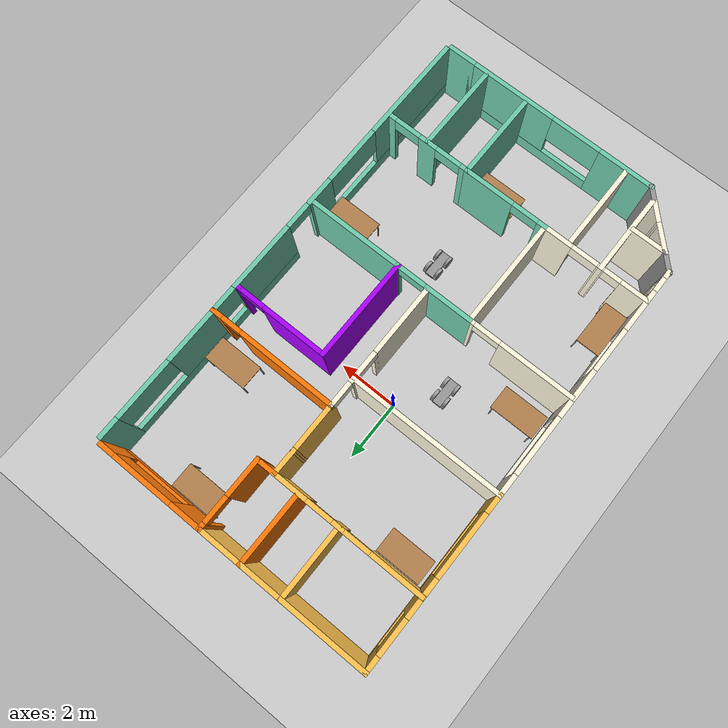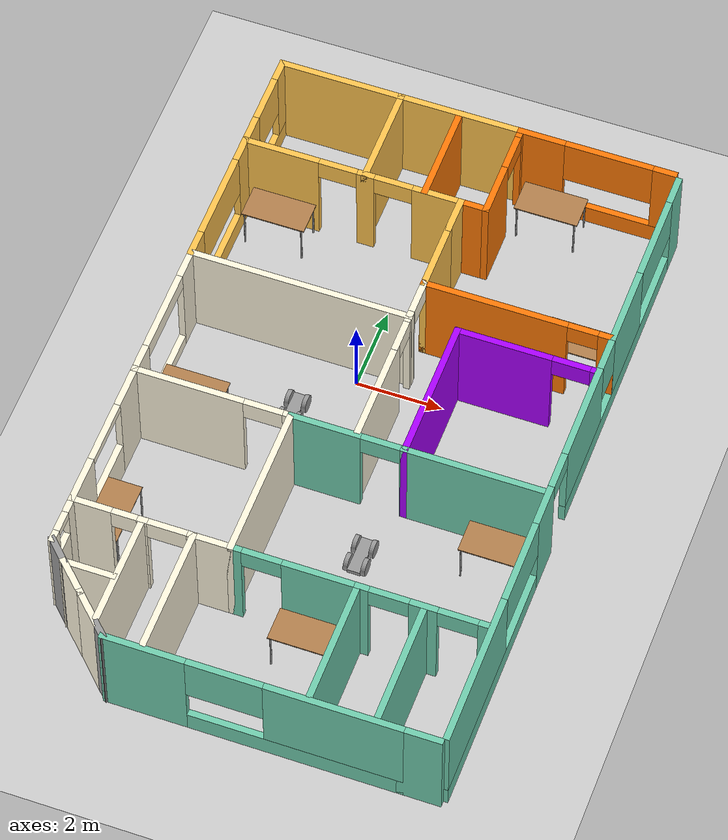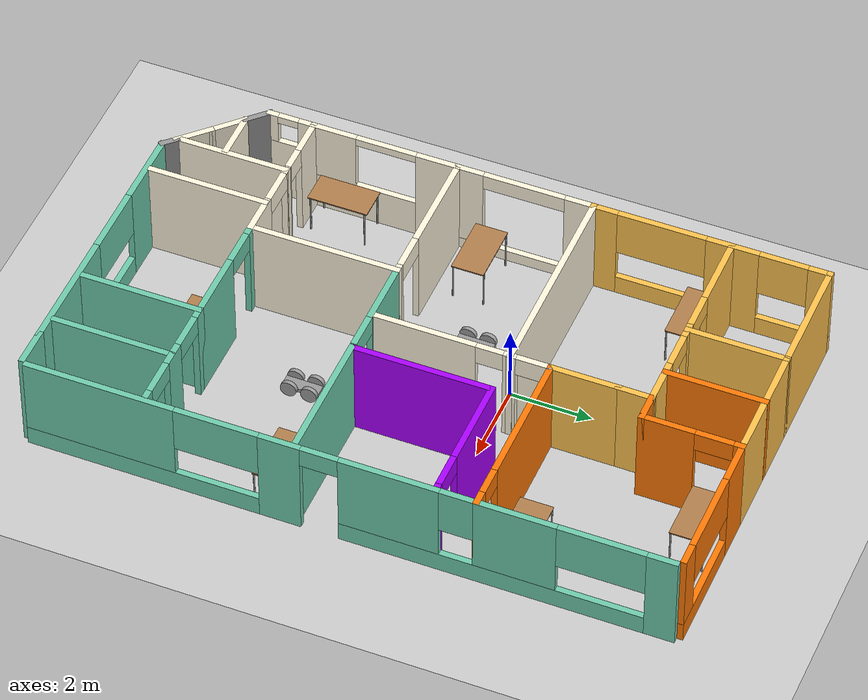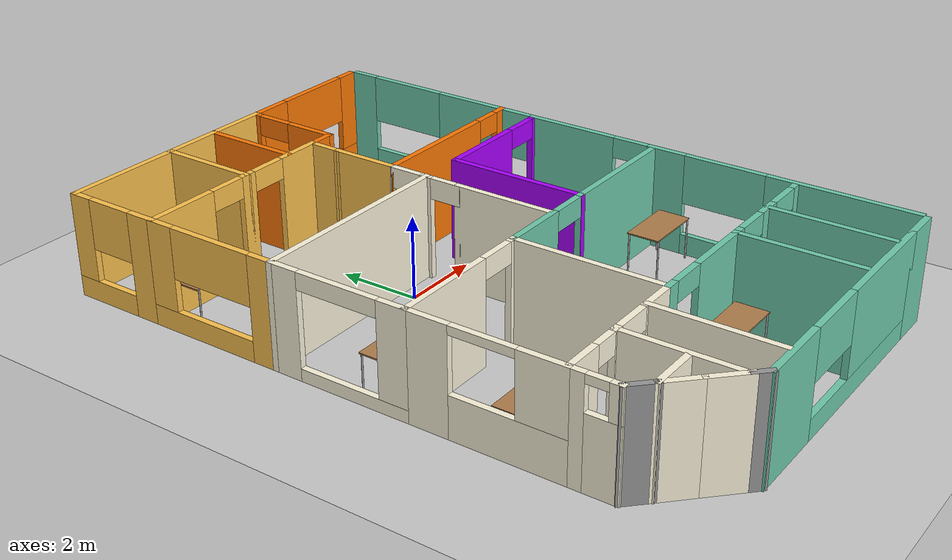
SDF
<sdf version="1.6">
 <world name="default">
  <plugin name="welcome" filename="libwelcome.so"/>
  <light name="sun" type="directional">
   <pose>0 0 10 0 -0 0</pose>
   <diffuse>0.8 0.8 0.8 1</diffuse>
   <specular>0.2 0.2 0.2 1</specular>
   <attenuation>
    <range>1000</range>
    <constant>0.9</constant>
    <linear>0.01</linear>
    <quadratic>0.001</quadratic>
   </attenuation>
   <direction>-0.5 0.1 -0.9</direction>
  </light>
  <model name="ground_plane">
   <static>1</static>
   <link name="link">
    <collision name="collision">
     <geometry><plane><normal>0 0 1</normal><size>100 100</size></plane></geometry>
     <surface><friction><ode><mu>100</mu><mu2>50</mu2></ode></friction></surface>
    </collision>
    <visual name="visual">
     <cast_shadows>0</cast_shadows>
     <geometry><plane><normal>0 0 1</normal><size>100 100</size></plane></geometry>
     <material>
      <script><uri>file://media/materials/scripts/gazebo.material</uri><name>Gazebo/Grey</name></script>
     </material>
    </visual>
   </link>
  </model>
  <gravity>0 0 -9.8</gravity>
  <magnetic_field>6e-06 2.3e-05 -4.2e-05</magnetic_field>
  <atmosphere type="adiabatic"/>
  <physics name="default_physics" default="0" type="ode">
   <max_step_size>0.001</max_step_size>
   <real_time_factor>1</real_time_factor>
   <real_time_update_rate>1000</real_time_update_rate>
  </physics>
  <scene><ambient>0.4 0.4 0.4 1</ambient><background>0.7 0.7 0.7 1</background><shadows>1</shadows></scene>
  <spherical_coordinates>
   <surface_model>EARTH_WGS84</surface_model>
   <latitude_deg>0</latitude_deg>
   <longitude_deg>0</longitude_deg>
   <elevation>0</elevation>
   <heading_deg>0</heading_deg>
  </spherical_coordinates>
  <model name="Building">
   <pose>0.68406 -1.71329 0 0 -0 0</pose>
   <link name="Wall_103">
    <collision name="Wall_103_Collision">
     <geometry><box><size>2.75 0.15 2.5</size></box></geometry>
     <pose>0 0 1.25 0 -0 0</pose>
    </collision>
    <visual name="Wall_103_Visual">
     <pose>0 0 1.25 0 -0 0</pose>
     <geometry><box><size>2.75 0.15 2.5</size></box></geometry>
     <material>
      <script><uri>file://media/materials/scripts/gazebo.material</uri><name>Gazebo/Grey</name></script>
      <ambient>1 0.968627 0.870588 1</ambient>
     </material>
     <meta><layer>0</layer></meta>
    </visual>
    <pose>-3.10082 -6.11639 0 0 -0 1.5708</pose>
   </link>
   <link name="Wall_105">
    <collision name="Wall_105_Collision">
     <geometry><box><size>1.0071 0.15 2.5</size></box></geometry>
     <pose>0 0 1.25 0 -0 0</pose>
    </collision>
    <visual name="Wall_105_Visual">
     <pose>0 0 1.25 0 -0 0</pose>
     <geometry><box><size>1.0071 0.15 2.5</size></box></geometry>
     <material>
      <script><uri>file://media/materials/scripts/gazebo.material</uri><name>Gazebo/Grey</name></script>
      <ambient>1 0.968627 0.870588 1</ambient>
     </material>
     <meta><layer>0</layer></meta>
    </visual>
    <pose>-3.96602 -6.6535 0 0 0 -0.777148</pose>
   </link>
   <link name="Wall_106">
    <collision name="Wall_106_Collision">
     <geometry><box><size>1 0.15 2.5</size></box></geometry>
     <pose>0 0 1.25 0 -0 0</pose>
    </collision>
    <visual name="Wall_106_Visual">
     <pose>0 0 1.25 0 -0 0</pose>
     <geometry><box><size>1 0.15 2.5</size></box></geometry>
     <material>
      <script><uri>file://media/materials/scripts/gazebo.material</uri><name>Gazebo/Grey</name></script>
      <ambient>1 0.968627 0.870588 1</ambient>
     </material>
     <meta><layer>0</layer></meta>
    </visual>
    <pose>-3.35998 -7.25454 0 0 0 -0.785398</pose>
   </link>
   <link name="Wall_107">
    <collision name="Wall_107_Collision">
     <geometry><box><size>0.5 0.15 2.5</size></box></geometry>
     <pose>0 0 1.25 0 -0 0</pose>
    </collision>
    <visual name="Wall_107_Visual">
     <pose>0 0 1.25 0 -0 0</pose>
     <geometry><box><size>0.5 0.15 2.5</size></box></geometry>
     <material>
      <script><uri>file://media/materials/scripts/gazebo.material</uri><name>Gazebo/Grey</name></script>
      <ambient>1 1 1 1</ambient>
     </material>
     <meta><layer>0</layer></meta>
    </visual>
    <pose>-2.93571 -7.6788 0 0 0 -0.785398</pose>
   </link>
   <link name="Wall_108">
    <pose>0.488031 -7.80255 0 0 -0 0</pose>
    <visual name="Wall_108_Visual_0">
     <pose>-2.41446 0 1.25 0 -0 0</pose>
     <geometry><box><size>1.92107 0.15 2.5</size></box></geometry>
     <material>
      <script><uri>file://media/materials/scripts/gazebo.material</uri><name>Gazebo/Grey</name></script>
      <ambient>0.435294 0.796078 0.67451 1</ambient>
     </material>
     <meta><layer>0</layer></meta>
    </visual>
    <collision name="Wall_108_Collision_0">
     <geometry><box><size>1.92107 0.15 2.5</size></box></geometry>
     <pose>-2.41446 0 1.25 0 -0 0</pose>
    </collision>
    <visual name="Wall_108_Visual_1">
     <pose>0.960535 0 0.25 0 -0 0</pose>
     <geometry><box><size>4.82893 0.15 0.5</size></box></geometry>
     <material>
      <script><uri>file://media/materials/scripts/gazebo.material</uri><name>Gazebo/Grey</name></script>
      <ambient>0.435294 0.796078 0.67451 1</ambient>
     </material>
     <meta><layer>0</layer></meta>
    </visual>
    <collision name="Wall_108_Collision_1">
     <geometry><box><size>4.82893 0.15 0.5</size></box></geometry>
     <pose>0.960535 0 0.25 0 -0 0</pose>
    </collision>
    <visual name="Wall_108_Visual_2">
     <pose>1.82294 0 1.5 0 -0 0</pose>
     <geometry><box><size>3.10413 0.15 2</size></box></geometry>
     <material>
      <script><uri>file://media/materials/scripts/gazebo.material</uri><name>Gazebo/Grey</name></script>
      <ambient>0.435294 0.796078 0.67451 1</ambient>
     </material>
     <meta><layer>0</layer></meta>
    </visual>
    <collision name="Wall_108_Collision_2">
     <geometry><box><size>3.10413 0.15 2</size></box></geometry>
     <pose>1.82294 0 1.5 0 -0 0</pose>
    </collision>
    <visual name="Wall_108_Visual_3">
     <pose>-0.591528 0 1.9 0 -0 0</pose>
     <geometry><box><size>1.7248 0.15 1.2</size></box></geometry>
     <material>
      <script><uri>file://media/materials/scripts/gazebo.material</uri><name>Gazebo/Grey</name></script>
      <ambient>0.435294 0.796078 0.67451 1</ambient>
     </material>
     <meta><layer>0</layer></meta>
    </visual>
    <collision name="Wall_108_Collision_3">
     <geometry><box><size>1.7248 0.15 1.2</size></box></geometry>
     <pose>-0.591528 0 1.9 0 -0 0</pose>
    </collision>
   </link>
   <link name="Wall_112">
    <collision name="Wall_112_Collision">
     <geometry><box><size>1 0.15 2.5</size></box></geometry>
     <pose>0 0 1.25 0 -0 0</pose>
    </collision>
    <visual name="Wall_112_Visual">
     <pose>0 0 1.25 0 -0 0</pose>
     <geometry><box><size>1 0.15 2.5</size></box></geometry>
     <material>
      <script><uri>file://media/materials/scripts/gazebo.material</uri><name>Gazebo/Grey</name></script>
      <ambient>0.435294 0.796078 0.67451 1</ambient>
     </material>
     <meta><layer>0</layer></meta>
    </visual>
    <pose>4.21303 -7.80255 0 0 -0 0</pose>
   </link>
   <link name="Wall_115">
    <pose>-4.7058 3.80629 0 0 -0 1.5708</pose>
    <visual name="Wall_115_Visual_0">
     <pose>-1.41322 0 1.25 0 -0 0</pose>
     <geometry><box><size>0.673551 0.15 2.5</size></box></geometry>
     <material>
      <script><uri>file://media/materials/scripts/gazebo.material</uri><name>Gazebo/Grey</name></script>
      <ambient>1 0.764706 0.305882 1</ambient>
     </material>
     <meta><layer>0</layer></meta>
    </visual>
    <collision name="Wall_115_Collision_0">
     <geometry><box><size>0.673551 0.15 2.5</size></box></geometry>
     <pose>-1.41322 0 1.25 0 -0 0</pose>
    </collision>
    <visual name="Wall_115_Visual_1">
     <pose>0.336776 0 0.25 0 -0 0</pose>
     <geometry><box><size>2.82645 0.15 0.5</size></box></geometry>
     <material>
      <script><uri>file://media/materials/scripts/gazebo.material</uri><name>Gazebo/Grey</name></script>
      <ambient>1 0.764706 0.305882 1</ambient>
     </material>
     <meta><layer>0</layer></meta>
    </visual>
    <collision name="Wall_115_Collision_1">
     <geometry><box><size>2.82645 0.15 0.5</size></box></geometry>
     <pose>0.336776 0 0.25 0 -0 0</pose>
    </collision>
    <visual name="Wall_115_Visual_2">
     <pose>1.40974 0 1.5 0 -0 0</pose>
     <geometry><box><size>0.680513 0.15 2</size></box></geometry>
     <material>
      <script><uri>file://media/materials/scripts/gazebo.material</uri><name>Gazebo/Grey</name></script>
      <ambient>1 0.764706 0.305882 1</ambient>
     </material>
     <meta><layer>0</layer></meta>
    </visual>
    <collision name="Wall_115_Collision_2">
     <geometry><box><size>0.680513 0.15 2</size></box></geometry>
     <pose>1.40974 0 1.5 0 -0 0</pose>
    </collision>
    <visual name="Wall_115_Visual_3">
     <pose>-0.003481 0 1.9 0 -0 0</pose>
     <geometry><box><size>2.14594 0.15 1.2</size></box></geometry>
     <material>
      <script><uri>file://media/materials/scripts/gazebo.material</uri><name>Gazebo/Grey</name></script>
      <ambient>1 0.764706 0.305882 1</ambient>
     </material>
     <meta><layer>0</layer></meta>
    </visual>
    <collision name="Wall_115_Collision_3">
     <geometry><box><size>2.14594 0.15 1.2</size></box></geometry>
     <pose>-0.003481 0 1.9 0 -0 0</pose>
    </collision>
   </link>
   <link name="Wall_116">
    <pose>-2.1558 5.48129 0 0 -0 0</pose>
    <visual name="Wall_116_Visual_0">
     <pose>-1.70501 0 1.25 0 -0 0</pose>
     <geometry><box><size>1.83998 0.15 2.5</size></box></geometry>
     <material>
      <script><uri>file://media/materials/scripts/gazebo.material</uri><name>Gazebo/Grey</name></script>
      <ambient>1 0.764706 0.305882 1</ambient>
     </material>
     <meta><layer>0</layer></meta>
    </visual>
    <collision name="Wall_116_Collision_0">
     <geometry><box><size>1.83998 0.15 2.5</size></box></geometry>
     <pose>-1.70501 0 1.25 0 -0 0</pose>
    </collision>
    <visual name="Wall_116_Visual_1">
     <pose>0.319979 0 1.25 0 -0 0</pose>
     <geometry><box><size>0.41 0.15 2.5</size></box></geometry>
     <material>
      <script><uri>file://media/materials/scripts/gazebo.material</uri><name>Gazebo/Grey</name></script>
      <ambient>1 0.764706 0.305882 1</ambient>
     </material>
     <meta><layer>0</layer></meta>
    </visual>
    <collision name="Wall_116_Collision_1">
     <geometry><box><size>0.41 0.15 2.5</size></box></geometry>
     <pose>0.319979 0 1.25 0 -0 0</pose>
    </collision>
    <visual name="Wall_116_Visual_2">
     <pose>2.02499 0 1.25 0 -0 0</pose>
     <geometry><box><size>1.20002 0.15 2.5</size></box></geometry>
     <material>
      <script><uri>file://media/materials/scripts/gazebo.material</uri><name>Gazebo/Grey</name></script>
      <ambient>1 0.764706 0.305882 1</ambient>
     </material>
     <meta><layer>0</layer></meta>
    </visual>
    <collision name="Wall_116_Collision_2">
     <geometry><box><size>1.20002 0.15 2.5</size></box></geometry>
     <pose>2.02499 0 1.25 0 -0 0</pose>
    </collision>
    <visual name="Wall_116_Visual_3">
     <pose>-0.335021 0 2.25 0 -0 0</pose>
     <geometry><box><size>0.9 0.15 0.5</size></box></geometry>
     <material>
      <script><uri>file://media/materials/scripts/gazebo.material</uri><name>Gazebo/Grey</name></script>
      <ambient>1 0.764706 0.305882 1</ambient>
     </material>
     <meta><layer>0</layer></meta>
    </visual>
    <collision name="Wall_116_Collision_3">
     <geometry><box><size>0.9 0.15 0.5</size></box></geometry>
     <pose>-0.335021 0 2.25 0 -0 0</pose>
    </collision>
    <visual name="Wall_116_Visual_4">
     <pose>0.974979 0 2.25 0 -0 0</pose>
     <geometry><box><size>0.9 0.15 0.5</size></box></geometry>
     <material>
      <script><uri>file://media/materials/scripts/gazebo.material</uri><name>Gazebo/Grey</name></script>
      <ambient>1 0.764706 0.305882 1</ambient>
     </material>
     <meta><layer>0</layer></meta>
    </visual>
    <collision name="Wall_116_Collision_4">
     <geometry><box><size>0.9 0.15 0.5</size></box></geometry>
     <pose>0.974979 0 2.25 0 -0 0</pose>
    </collision>
   </link>
   <link name="Wall_117">
    <collision name="Wall_117_Collision">
     <geometry><box><size>0.939813 0.15 2.5</size></box></geometry>
     <pose>0 0 1.25 0 -0 0</pose>
    </collision>
    <visual name="Wall_117_Visual">
     <pose>0 0 1.25 0 -0 0</pose>
     <geometry><box><size>0.939813 0.15 2.5</size></box></geometry>
     <material>
      <script><uri>file://media/materials/scripts/gazebo.material</uri><name>Gazebo/Grey</name></script>
      <ambient>1 0.764706 0.305882 1</ambient>
     </material>
     <meta><layer>0</layer></meta>
    </visual>
    <pose>0.390532 5.0864 0 0 0 -1.58008</pose>
   </link>
   <link name="Wall_119">
    <pose>-4.7058 6.65629 0 0 -0 1.5708</pose>
    <visual name="Wall_119_Visual_0">
     <pose>-0.875559 0 1.25 0 -0 0</pose>
     <geometry><box><size>0.748882 0.15 2.5</size></box></geometry>
     <material>
      <script><uri>file://media/materials/scripts/gazebo.material</uri><name>Gazebo/Grey</name></script>
      <ambient>1 0.764706 0.305882 1</ambient>
     </material>
     <meta><layer>0</layer></meta>
    </visual>
    <collision name="Wall_119_Collision_0">
     <geometry><box><size>0.748882 0.15 2.5</size></box></geometry>
     <pose>-0.875559 0 1.25 0 -0 0</pose>
    </collision>
    <visual name="Wall_119_Visual_1">
     <pose>0.374441 0 0.25 0 -0 0</pose>
     <geometry><box><size>1.75112 0.15 0.5</size></box></geometry>
     <material>
      <script><uri>file://media/materials/scripts/gazebo.material</uri><name>Gazebo/Grey</name></script>
      <ambient>1 0.764706 0.305882 1</ambient>
     </material>
     <meta><layer>0</layer></meta>
    </visual>
    <collision name="Wall_119_Collision_1">
     <geometry><box><size>1.75112 0.15 0.5</size></box></geometry>
     <pose>0.374441 0 0.25 0 -0 0</pose>
    </collision>
    <visual name="Wall_119_Visual_2">
     <pose>0.959696 0 1.5 0 -0 0</pose>
     <geometry><box><size>0.580608 0.15 2</size></box></geometry>
     <material>
      <script><uri>file://media/materials/scripts/gazebo.material</uri><name>Gazebo/Grey</name></script>
      <ambient>1 0.764706 0.305882 1</ambient>
     </material>
     <meta><layer>0</layer></meta>
    </visual>
    <collision name="Wall_119_Collision_2">
     <geometry><box><size>0.580608 0.15 2</size></box></geometry>
     <pose>0.959696 0 1.5 0 -0 0</pose>
    </collision>
    <visual name="Wall_119_Visual_3">
     <pose>0.084137 0 1.9 0 -0 0</pose>
     <geometry><box><size>1.17051 0.15 1.2</size></box></geometry>
     <material>
      <script><uri>file://media/materials/scripts/gazebo.material</uri><name>Gazebo/Grey</name></script>
      <ambient>1 0.764706 0.305882 1</ambient>
     </material>
     <meta><layer>0</layer></meta>
    </visual>
    <collision name="Wall_119_Collision_3">
     <geometry><box><size>1.17051 0.15 1.2</size></box></geometry>
     <pose>0.084137 0 1.9 0 -0 0</pose>
    </collision>
   </link>
   <link name="Wall_120">
    <collision name="Wall_120_Collision">
     <geometry><box><size>3 0.15 2.5</size></box></geometry>
     <pose>0 0 1.25 0 -0 0</pose>
    </collision>
    <visual name="Wall_120_Visual">
     <pose>0 0 1.25 0 -0 0</pose>
     <geometry><box><size>3 0.15 2.5</size></box></geometry>
     <material>
      <script><uri>file://media/materials/scripts/gazebo.material</uri><name>Gazebo/Grey</name></script>
      <ambient>1 0.764706 0.305882 1</ambient>
     </material>
     <meta><layer>0</layer></meta>
    </visual>
    <pose>-3.2808 7.83129 0 0 -0 0</pose>
   </link>
   <link name="Wall_121">
    <collision name="Wall_121_Collision">
     <geometry><box><size>2.5 0.15 2.5</size></box></geometry>
     <pose>0 0 1.25 0 -0 0</pose>
    </collision>
    <visual name="Wall_121_Visual">
     <pose>0 0 1.25 0 -0 0</pose>
     <geometry><box><size>2.5 0.15 2.5</size></box></geometry>
     <material>
      <script><uri>file://media/materials/scripts/gazebo.material</uri><name>Gazebo/Grey</name></script>
      <ambient>1 0.764706 0.305882 1</ambient>
     </material>
     <meta><layer>0</layer></meta>
    </visual>
    <pose>-1.8558 6.65629 0 0 0 -1.5708</pose>
   </link>
   <link name="Wall_123">
    <collision name="Wall_123_Collision">
     <geometry><box><size>0.75 0.15 2.5</size></box></geometry>
     <pose>0 0 1.25 0 -0 0</pose>
    </collision>
    <visual name="Wall_123_Visual">
     <pose>0 0 1.25 0 -0 0</pose>
     <geometry><box><size>0.75 0.15 2.5</size></box></geometry>
     <material>
      <script><uri>file://media/materials/scripts/gazebo.material</uri><name>Gazebo/Grey</name></script>
      <ambient>0.996078 0.47451 0.0196078 1</ambient>
     </material>
     <meta><layer>0</layer></meta>
    </visual>
    <pose>0.694198 5.48129 0 0 -0 0</pose>
   </link>
   <link name="Wall_124">
    <pose>0.994198 6.65629 0 0 -0 1.5708</pose>
    <visual name="Wall_124_Visual_0">
     <pose>-0.586337 0 1.25 0 -0 0</pose>
     <geometry><box><size>1.32733 0.15 2.5</size></box></geometry>
     <material>
      <script><uri>file://media/materials/scripts/gazebo.material</uri><name>Gazebo/Grey</name></script>
      <ambient>0.996078 0.47451 0.0196078 1</ambient>
     </material>
     <meta><layer>0</layer></meta>
    </visual>
    <collision name="Wall_124_Collision_0">
     <geometry><box><size>1.32733 0.15 2.5</size></box></geometry>
     <pose>-0.586337 0 1.25 0 -0 0</pose>
    </collision>
    <visual name="Wall_124_Visual_1">
     <pose>1.11366 0 1.25 0 -0 0</pose>
     <geometry><box><size>0.272675 0.15 2.5</size></box></geometry>
     <material>
      <script><uri>file://media/materials/scripts/gazebo.material</uri><name>Gazebo/Grey</name></script>
      <ambient>0.996078 0.47451 0.0196078 1</ambient>
     </material>
     <meta><layer>0</layer></meta>
    </visual>
    <collision name="Wall_124_Collision_1">
     <geometry><box><size>0.272675 0.15 2.5</size></box></geometry>
     <pose>1.11366 0 1.25 0 -0 0</pose>
    </collision>
    <visual name="Wall_124_Visual_2">
     <pose>0.527325 0 2.25 0 -0 0</pose>
     <geometry><box><size>0.9 0.15 0.5</size></box></geometry>
     <material>
      <script><uri>file://media/materials/scripts/gazebo.material</uri><name>Gazebo/Grey</name></script>
      <ambient>0.996078 0.47451 0.0196078 1</ambient>
     </material>
     <meta><layer>0</layer></meta>
    </visual>
    <collision name="Wall_124_Collision_2">
     <geometry><box><size>0.9 0.15 0.5</size></box></geometry>
     <pose>0.527325 0 2.25 0 -0 0</pose>
    </collision>
   </link>
   <link name="Wall_125">
    <collision name="Wall_125_Collision">
     <geometry><box><size>3 0.15 2.5</size></box></geometry>
     <pose>0 0 1.25 0 -0 0</pose>
    </collision>
    <visual name="Wall_125_Visual">
     <pose>0 0 1.25 0 -0 0</pose>
     <geometry><box><size>3 0.15 2.5</size></box></geometry>
     <material>
      <script><uri>file://media/materials/scripts/gazebo.material</uri><name>Gazebo/Grey</name></script>
      <ambient>1 0.764706 0.305882 1</ambient>
     </material>
     <meta><layer>0</layer></meta>
    </visual>
    <pose>-0.430802 7.83129 0 0 0 -3.14159</pose>
   </link>
   <link name="Wall_127">
    <pose>2.7942 7.83129 0 0 -0 0</pose>
    <visual name="Wall_127_Visual_0">
     <pose>-1.31004 0 1.25 0 -0 0</pose>
     <geometry><box><size>1.12992 0.15 2.5</size></box></geometry>
     <material>
      <script><uri>file://media/materials/scripts/gazebo.material</uri><name>Gazebo/Grey</name></script>
      <ambient>0.996078 0.47451 0.0196078 1</ambient>
     </material>
     <meta><layer>0</layer></meta>
    </visual>
    <collision name="Wall_127_Collision_0">
     <geometry><box><size>1.12992 0.15 2.5</size></box></geometry>
     <pose>-1.31004 0 1.25 0 -0 0</pose>
    </collision>
    <visual name="Wall_127_Visual_1">
     <pose>0.564959 0 0.25 0 -0 0</pose>
     <geometry><box><size>2.62008 0.15 0.5</size></box></geometry>
     <material>
      <script><uri>file://media/materials/scripts/gazebo.material</uri><name>Gazebo/Grey</name></script>
      <ambient>0.996078 0.47451 0.0196078 1</ambient>
     </material>
     <meta><layer>0</layer></meta>
    </visual>
    <collision name="Wall_127_Collision_1">
     <geometry><box><size>2.62008 0.15 0.5</size></box></geometry>
     <pose>0.564959 0 0.25 0 -0 0</pose>
    </collision>
    <visual name="Wall_127_Visual_2">
     <pose>1.59653 0 1.5 0 -0 0</pose>
     <geometry><box><size>0.556934 0.15 2</size></box></geometry>
     <material>
      <script><uri>file://media/materials/scripts/gazebo.material</uri><name>Gazebo/Grey</name></script>
      <ambient>0.996078 0.47451 0.0196078 1</ambient>
     </material>
     <meta><layer>0</layer></meta>
    </visual>
    <collision name="Wall_127_Collision_2">
     <geometry><box><size>0.556934 0.15 2</size></box></geometry>
     <pose>1.59653 0 1.5 0 -0 0</pose>
    </collision>
    <visual name="Wall_127_Visual_3">
     <pose>0.286491 0 1.9 0 -0 0</pose>
     <geometry><box><size>2.06315 0.15 1.2</size></box></geometry>
     <material>
      <script><uri>file://media/materials/scripts/gazebo.material</uri><name>Gazebo/Grey</name></script>
      <ambient>0.996078 0.47451 0.0196078 1</ambient>
     </material>
     <meta><layer>0</layer></meta>
    </visual>
    <collision name="Wall_127_Collision_3">
     <geometry><box><size>2.06315 0.15 1.2</size></box></geometry>
     <pose>0.286491 0 1.9 0 -0 0</pose>
    </collision>
   </link>
   <link name="Wall_129">
    <collision name="Wall_129_Collision">
     <geometry><box><size>2.5 0.15 2.5</size></box></geometry>
     <pose>0 0 1.25 0 -0 0</pose>
    </collision>
    <visual name="Wall_129_Visual">
     <pose>0 0 1.25 0 -0 0</pose>
     <geometry><box><size>2.5 0.15 2.5</size></box></geometry>
     <material>
      <script><uri>file://media/materials/scripts/gazebo.material</uri><name>Gazebo/Grey</name></script>
      <ambient>0.996078 0.47451 0.0196078 1</ambient>
     </material>
     <meta><layer>0</layer></meta>
    </visual>
    <pose>-0.450823 6.65861 0 0 -0 1.5708</pose>
   </link>
   <link name="Wall_131">
    <pose>0.319198 -4.81871 0 0 -0 0</pose>
    <visual name="Wall_131_Visual_0">
     <pose>-1.33501 0 1.25 0 -0 0</pose>
     <geometry><box><size>0.329979 0.15 2.5</size></box></geometry>
     <material>
      <script><uri>file://media/materials/scripts/gazebo.material</uri><name>Gazebo/Grey</name></script>
      <ambient>0.435294 0.796078 0.67451 1</ambient>
     </material>
     <meta><layer>0</layer></meta>
    </visual>
    <collision name="Wall_131_Collision_0">
     <geometry><box><size>0.329979 0.15 2.5</size></box></geometry>
     <pose>-1.33501 0 1.25 0 -0 0</pose>
    </collision>
    <visual name="Wall_131_Visual_1">
     <pose>0.614989 0 1.25 0 -0 0</pose>
     <geometry><box><size>1.77002 0.15 2.5</size></box></geometry>
     <material>
      <script><uri>file://media/materials/scripts/gazebo.material</uri><name>Gazebo/Grey</name></script>
      <ambient>0.435294 0.796078 0.67451 1</ambient>
     </material>
     <meta><layer>0</layer></meta>
    </visual>
    <collision name="Wall_131_Collision_1">
     <geometry><box><size>1.77002 0.15 2.5</size></box></geometry>
     <pose>0.614989 0 1.25 0 -0 0</pose>
    </collision>
    <visual name="Wall_131_Visual_2">
     <pose>-0.720021 0 2.25 0 -0 0</pose>
     <geometry><box><size>0.9 0.15 0.5</size></box></geometry>
     <material>
      <script><uri>file://media/materials/scripts/gazebo.material</uri><name>Gazebo/Grey</name></script>
      <ambient>0.435294 0.796078 0.67451 1</ambient>
     </material>
     <meta><layer>0</layer></meta>
    </visual>
    <collision name="Wall_131_Collision_2">
     <geometry><box><size>0.9 0.15 0.5</size></box></geometry>
     <pose>-0.720021 0 2.25 0 -0 0</pose>
    </collision>
   </link>
   <link name="Wall_132">
    <collision name="Wall_132_Collision">
     <geometry><box><size>3 0.15 2.5</size></box></geometry>
     <pose>0 0 1.25 0 -0 0</pose>
    </collision>
    <visual name="Wall_132_Visual">
     <pose>0 0 1.25 0 -0 0</pose>
     <geometry><box><size>3 0.15 2.5</size></box></geometry>
     <material>
      <script><uri>file://media/materials/scripts/gazebo.material</uri><name>Gazebo/Grey</name></script>
      <ambient>0.435294 0.796078 0.67451 1</ambient>
     </material>
     <meta><layer>0</layer></meta>
    </visual>
    <pose>1.7442 -6.24371 0 0 0 -1.5708</pose>
   </link>
   <link name="Wall_135">
    <pose>3.1692 -4.81871 0 0 -0 0</pose>
    <visual name="Wall_135_Visual_0">
     <pose>-1.33501 0 1.25 0 -0 0</pose>
     <geometry><box><size>0.329979 0.15 2.5</size></box></geometry>
     <material>
      <script><uri>file://media/materials/scripts/gazebo.material</uri><name>Gazebo/Grey</name></script>
      <ambient>0.435294 0.796078 0.67451 1</ambient>
     </material>
     <meta><layer>0</layer></meta>
    </visual>
    <collision name="Wall_135_Collision_0">
     <geometry><box><size>0.329979 0.15 2.5</size></box></geometry>
     <pose>-1.33501 0 1.25 0 -0 0</pose>
    </collision>
    <visual name="Wall_135_Visual_1">
     <pose>0.044978 0 1.25 0 -0 0</pose>
     <geometry><box><size>0.63 0.15 2.5</size></box></geometry>
     <material>
      <script><uri>file://media/materials/scripts/gazebo.material</uri><name>Gazebo/Grey</name></script>
      <ambient>0.435294 0.796078 0.67451 1</ambient>
     </material>
     <meta><layer>0</layer></meta>
    </visual>
    <collision name="Wall_135_Collision_1">
     <geometry><box><size>0.63 0.15 2.5</size></box></geometry>
     <pose>0.044978 0 1.25 0 -0 0</pose>
    </collision>
    <visual name="Wall_135_Visual_2">
     <pose>1.37999 0 1.25 0 -0 0</pose>
     <geometry><box><size>0.240022 0.15 2.5</size></box></geometry>
     <material>
      <script><uri>file://media/materials/scripts/gazebo.material</uri><name>Gazebo/Grey</name></script>
      <ambient>0.435294 0.796078 0.67451 1</ambient>
     </material>
     <meta><layer>0</layer></meta>
    </visual>
    <collision name="Wall_135_Collision_2">
     <geometry><box><size>0.240022 0.15 2.5</size></box></geometry>
     <pose>1.37999 0 1.25 0 -0 0</pose>
    </collision>
    <visual name="Wall_135_Visual_3">
     <pose>-0.720021 0 2.25 0 -0 0</pose>
     <geometry><box><size>0.9 0.15 0.5</size></box></geometry>
     <material>
      <script><uri>file://media/materials/scripts/gazebo.material</uri><name>Gazebo/Grey</name></script>
      <ambient>0.435294 0.796078 0.67451 1</ambient>
     </material>
     <meta><layer>0</layer></meta>
    </visual>
    <collision name="Wall_135_Collision_3">
     <geometry><box><size>0.9 0.15 0.5</size></box></geometry>
     <pose>-0.720021 0 2.25 0 -0 0</pose>
    </collision>
    <visual name="Wall_135_Visual_4">
     <pose>0.809978 0 2.25 0 -0 0</pose>
     <geometry><box><size>0.9 0.15 0.5</size></box></geometry>
     <material>
      <script><uri>file://media/materials/scripts/gazebo.material</uri><name>Gazebo/Grey</name></script>
      <ambient>0.435294 0.796078 0.67451 1</ambient>
     </material>
     <meta><layer>0</layer></meta>
    </visual>
    <collision name="Wall_135_Collision_4">
     <geometry><box><size>0.9 0.15 0.5</size></box></geometry>
     <pose>0.809978 0 2.25 0 -0 0</pose>
    </collision>
   </link>
   <link name="Wall_137">
    <collision name="Wall_137_Collision">
     <geometry><box><size>3 0.15 2.5</size></box></geometry>
     <pose>0 0 1.25 0 -0 0</pose>
    </collision>
    <visual name="Wall_137_Visual">
     <pose>0 0 1.25 0 -0 0</pose>
     <geometry><box><size>3 0.15 2.5</size></box></geometry>
     <material>
      <script><uri>file://media/materials/scripts/gazebo.material</uri><name>Gazebo/Grey</name></script>
      <ambient>0.435294 0.796078 0.67451 1</ambient>
     </material>
     <meta><layer>0</layer></meta>
    </visual>
    <pose>3.23918 -6.26139 0 0 0 -1.5708</pose>
   </link>
   <link name="Wall_23">
    <pose>0.386867 2.16651 0 0 0 -1.5708</pose>
    <visual name="Wall_23_Visual_0">
     <pose>-0.953706 0 1.25 0 -0 0</pose>
     <geometry><box><size>0.092589 0.15 2.5</size></box></geometry>
     <material>
      <script><uri>file://media/materials/scripts/gazebo.material</uri><name>Gazebo/Grey</name></script>
      <ambient>1 0.968627 0.870588 1</ambient>
     </material>
     <meta><layer>0</layer></meta>
    </visual>
    <collision name="Wall_23_Collision_0">
     <geometry><box><size>0.092589 0.15 2.5</size></box></geometry>
     <pose>-0.953706 0 1.25 0 -0 0</pose>
    </collision>
    <visual name="Wall_23_Visual_1">
     <pose>0.044331 0 1.25 0 -0 0</pose>
     <geometry><box><size>0.303484 0.15 2.5</size></box></geometry>
     <material>
      <script><uri>file://media/materials/scripts/gazebo.material</uri><name>Gazebo/Grey</name></script>
      <ambient>1 0.968627 0.870588 1</ambient>
     </material>
     <meta><layer>0</layer></meta>
    </visual>
    <collision name="Wall_23_Collision_1">
     <geometry><box><size>0.303484 0.15 2.5</size></box></geometry>
     <pose>0.044331 0 1.25 0 -0 0</pose>
    </collision>
    <visual name="Wall_23_Visual_2">
     <pose>0.998036 0 1.25 0 -0 0</pose>
     <geometry><box><size>0.003927 0.15 2.5</size></box></geometry>
     <material>
      <script><uri>file://media/materials/scripts/gazebo.material</uri><name>Gazebo/Grey</name></script>
      <ambient>1 0.968627 0.870588 1</ambient>
     </material>
     <meta><layer>0</layer></meta>
    </visual>
    <collision name="Wall_23_Collision_2">
     <geometry><box><size>0.003927 0.15 2.5</size></box></geometry>
     <pose>0.998036 0 1.25 0 -0 0</pose>
    </collision>
    <visual name="Wall_23_Visual_3">
     <pose>-0.507411 0 2.25 0 -0 0</pose>
     <geometry><box><size>0.8 0.15 0.5</size></box></geometry>
     <material>
      <script><uri>file://media/materials/scripts/gazebo.material</uri><name>Gazebo/Grey</name></script>
      <ambient>1 0.968627 0.870588 1</ambient>
     </material>
     <meta><layer>0</layer></meta>
    </visual>
    <collision name="Wall_23_Collision_3">
     <geometry><box><size>0.8 0.15 0.5</size></box></geometry>
     <pose>-0.507411 0 2.25 0 -0 0</pose>
    </collision>
    <visual name="Wall_23_Visual_4">
     <pose>0.596073 0 2.25 0 -0 0</pose>
     <geometry><box><size>0.8 0.15 0.5</size></box></geometry>
     <material>
      <script><uri>file://media/materials/scripts/gazebo.material</uri><name>Gazebo/Grey</name></script>
      <ambient>1 0.968627 0.870588 1</ambient>
     </material>
     <meta><layer>0</layer></meta>
    </visual>
    <collision name="Wall_23_Collision_4">
     <geometry><box><size>0.8 0.15 0.5</size></box></geometry>
     <pose>0.596073 0 2.25 0 -0 0</pose>
    </collision>
   </link>
   <link name="Wall_30">
    <collision name="Wall_30_Collision">
     <geometry><box><size>1.75 0.15 2.5</size></box></geometry>
     <pose>0 0 1.25 0 -0 0</pose>
    </collision>
    <visual name="Wall_30_Visual">
     <pose>0 0 1.25 0 -0 0</pose>
     <geometry><box><size>1.75 0.15 2.5</size></box></geometry>
     <material>
      <script><uri>file://media/materials/scripts/gazebo.material</uri><name>Gazebo/Grey</name></script>
      <ambient>1 0.764706 0.305882 1</ambient>
     </material>
     <meta><layer>0</layer></meta>
    </visual>
    <pose>0.386867 3.89151 0 0 -0 1.5708</pose>
   </link>
   <link name="Wall_36">
    <pose>4.73687 0.016508 0 0 0 -1.5708</pose>
    <visual name="Wall_36_Visual_0">
     <pose>-7.38566 0 1.25 0 -0 0</pose>
     <geometry><box><size>0.728677 0.15 2.5</size></box></geometry>
     <material>
      <script><uri>file://media/materials/scripts/gazebo.material</uri><name>Gazebo/Grey</name></script>
      <ambient>0.435294 0.796078 0.67451 1</ambient>
     </material>
     <meta><layer>0</layer></meta>
    </visual>
    <collision name="Wall_36_Collision_0">
     <geometry><box><size>0.728677 0.15 2.5</size></box></geometry>
     <pose>-7.38566 0 1.25 0 -0 0</pose>
    </collision>
    <visual name="Wall_36_Visual_1">
     <pose>1.57462 0 1.25 0 -0 0</pose>
     <geometry><box><size>1.00346 0.15 2.5</size></box></geometry>
     <material>
      <script><uri>file://media/materials/scripts/gazebo.material</uri><name>Gazebo/Grey</name></script>
      <ambient>0.435294 0.796078 0.67451 1</ambient>
     </material>
     <meta><layer>0</layer></meta>
    </visual>
    <collision name="Wall_36_Collision_1">
     <geometry><box><size>1.00346 0.15 2.5</size></box></geometry>
     <pose>1.57462 0 1.25 0 -0 0</pose>
    </collision>
    <visual name="Wall_36_Visual_2">
     <pose>-3.42421 0 0.25 0 -0 0</pose>
     <geometry><box><size>7.19422 0.15 0.5</size></box></geometry>
     <material>
      <script><uri>file://media/materials/scripts/gazebo.material</uri><name>Gazebo/Grey</name></script>
      <ambient>0.435294 0.796078 0.67451 1</ambient>
     </material>
     <meta><layer>0</layer></meta>
    </visual>
    <collision name="Wall_36_Collision_2">
     <geometry><box><size>7.19422 0.15 0.5</size></box></geometry>
     <pose>-3.42421 0 0.25 0 -0 0</pose>
    </collision>
    <visual name="Wall_36_Visual_3">
     <pose>4.91318 0 0.25 0 -0 0</pose>
     <geometry><box><size>5.67365 0.15 0.5</size></box></geometry>
     <material>
      <script><uri>file://media/materials/scripts/gazebo.material</uri><name>Gazebo/Grey</name></script>
      <ambient>0.435294 0.796078 0.67451 1</ambient>
     </material>
     <meta><layer>0</layer></meta>
    </visual>
    <collision name="Wall_36_Collision_3">
     <geometry><box><size>5.67365 0.15 0.5</size></box></geometry>
     <pose>4.91318 0 0.25 0 -0 0</pose>
    </collision>
    <visual name="Wall_36_Visual_4">
     <pose>-3.98224 0 1.5 0 -0 0</pose>
     <geometry><box><size>1.93682 0.15 2</size></box></geometry>
     <material>
      <script><uri>file://media/materials/scripts/gazebo.material</uri><name>Gazebo/Grey</name></script>
      <ambient>0.435294 0.796078 0.67451 1</ambient>
     </material>
     <meta><layer>0</layer></meta>
    </visual>
    <collision name="Wall_36_Collision_4">
     <geometry><box><size>1.93682 0.15 2</size></box></geometry>
     <pose>-3.98224 0 1.5 0 -0 0</pose>
    </collision>
    <visual name="Wall_36_Visual_5">
     <pose>-1.02047 0 1.5 0 -0 0</pose>
     <geometry><box><size>2.38673 0.15 2</size></box></geometry>
     <material>
      <script><uri>file://media/materials/scripts/gazebo.material</uri><name>Gazebo/Grey</name></script>
      <ambient>0.435294 0.796078 0.67451 1</ambient>
     </material>
     <meta><layer>0</layer></meta>
    </visual>
    <collision name="Wall_36_Collision_5">
     <geometry><box><size>2.38673 0.15 2</size></box></geometry>
     <pose>-1.02047 0 1.5 0 -0 0</pose>
    </collision>
    <visual name="Wall_36_Visual_6">
     <pose>-1.02047 0 1.5 0 -0 0</pose>
     <geometry><box><size>2.38673 0.15 2</size></box></geometry>
     <material>
      <script><uri>file://media/materials/scripts/gazebo.material</uri><name>Gazebo/Grey</name></script>
      <ambient>0.435294 0.796078 0.67451 1</ambient>
     </material>
     <meta><layer>0</layer></meta>
    </visual>
    <collision name="Wall_36_Collision_6">
     <geometry><box><size>2.38673 0.15 2</size></box></geometry>
     <pose>-1.02047 0 1.5 0 -0 0</pose>
    </collision>
    <visual name="Wall_36_Visual_7">
     <pose>5.92595 0 1.5 0 -0 0</pose>
     <geometry><box><size>3.64809 0.15 2</size></box></geometry>
     <material>
      <script><uri>file://media/materials/scripts/gazebo.material</uri><name>Gazebo/Grey</name></script>
      <ambient>0.435294 0.796078 0.67451 1</ambient>
     </material>
     <meta><layer>0</layer></meta>
    </visual>
    <collision name="Wall_36_Collision_7">
     <geometry><box><size>3.64809 0.15 2</size></box></geometry>
     <pose>5.92595 0 1.5 0 -0 0</pose>
    </collision>
    <visual name="Wall_36_Visual_8">
     <pose>-5.98599 0 1.9 0 -0 0</pose>
     <geometry><box><size>2.07067 0.15 1.2</size></box></geometry>
     <material>
      <script><uri>file://media/materials/scripts/gazebo.material</uri><name>Gazebo/Grey</name></script>
      <ambient>0.435294 0.796078 0.67451 1</ambient>
     </material>
     <meta><layer>0</layer></meta>
    </visual>
    <collision name="Wall_36_Collision_8">
     <geometry><box><size>2.07067 0.15 1.2</size></box></geometry>
     <pose>-5.98599 0 1.9 0 -0 0</pose>
    </collision>
    <visual name="Wall_36_Visual_9">
     <pose>3.08913 0 1.9 0 -0 0</pose>
     <geometry><box><size>2.02556 0.15 1.2</size></box></geometry>
     <material>
      <script><uri>file://media/materials/scripts/gazebo.material</uri><name>Gazebo/Grey</name></script>
      <ambient>0.435294 0.796078 0.67451 1</ambient>
     </material>
     <meta><layer>0</layer></meta>
    </visual>
    <collision name="Wall_36_Collision_9">
     <geometry><box><size>2.02556 0.15 1.2</size></box></geometry>
     <pose>3.08913 0 1.9 0 -0 0</pose>
    </collision>
    <visual name="Wall_36_Visual_10">
     <pose>-2.61383 0 1.9 0 -0 0</pose>
     <geometry><box><size>0.8 0.15 1.2</size></box></geometry>
     <material>
      <script><uri>file://media/materials/scripts/gazebo.material</uri><name>Gazebo/Grey</name></script>
      <ambient>0.435294 0.796078 0.67451 1</ambient>
     </material>
     <meta><layer>0</layer></meta>
    </visual>
    <collision name="Wall_36_Collision_10">
     <geometry><box><size>0.8 0.15 1.2</size></box></geometry>
     <pose>-2.61383 0 1.9 0 -0 0</pose>
    </collision>
    <visual name="Wall_36_Visual_11">
     <pose>0.622896 0 2.25 0 -0 0</pose>
     <geometry><box><size>0.9 0.15 0.5</size></box></geometry>
     <material>
      <script><uri>file://media/materials/scripts/gazebo.material</uri><name>Gazebo/Grey</name></script>
      <ambient>0.435294 0.796078 0.67451 1</ambient>
     </material>
     <meta><layer>0</layer></meta>
    </visual>
    <collision name="Wall_36_Collision_11">
     <geometry><box><size>0.9 0.15 0.5</size></box></geometry>
     <pose>0.622896 0 2.25 0 -0 0</pose>
    </collision>
    <visual name="Wall_36_Visual_12">
     <pose>0.622896 0 2.25 0 -0 0</pose>
     <geometry><box><size>0.9 0.15 0.5</size></box></geometry>
     <material>
      <script><uri>file://media/materials/scripts/gazebo.material</uri><name>Gazebo/Grey</name></script>
      <ambient>0.435294 0.796078 0.67451 1</ambient>
     </material>
     <meta><layer>0</layer></meta>
    </visual>
    <collision name="Wall_36_Collision_12">
     <geometry><box><size>0.9 0.15 0.5</size></box></geometry>
     <pose>0.622896 0 2.25 0 -0 0</pose>
    </collision>
   </link>
   <link name="Wall_42">
    <collision name="Wall_42_Collision">
     <geometry><box><size>5.25 0.15 2.5</size></box></geometry>
     <pose>0 0 1.25 0 -0 0</pose>
    </collision>
    <visual name="Wall_42_Visual">
     <pose>0 0 1.25 0 -0 0</pose>
     <geometry><box><size>5.25 0.15 2.5</size></box></geometry>
     <material>
      <script><uri>file://media/materials/scripts/gazebo.material</uri><name>Gazebo/Grey</name></script>
      <ambient>1 0.968627 0.870588 1</ambient>
     </material>
     <meta><layer>0</layer></meta>
    </visual>
    <pose>-2.1558 2.13129 0 0 -0 3.14159</pose>
   </link>
   <link name="Wall_45">
    <pose>-4.7058 0.456287 0 0 0 -1.5708</pose>
    <visual name="Wall_45_Visual_0">
     <pose>-1.36395 0 1.25 0 -0 0</pose>
     <geometry><box><size>0.772101 0.15 2.5</size></box></geometry>
     <material>
      <script><uri>file://media/materials/scripts/gazebo.material</uri><name>Gazebo/Grey</name></script>
      <ambient>1 0.968627 0.870588 1</ambient>
     </material>
     <meta><layer>0</layer></meta>
    </visual>
    <collision name="Wall_45_Collision_0">
     <geometry><box><size>0.772101 0.15 2.5</size></box></geometry>
     <pose>-1.36395 0 1.25 0 -0 0</pose>
    </collision>
    <visual name="Wall_45_Visual_1">
     <pose>0.386051 0 0.15 0 -0 0</pose>
     <geometry><box><size>2.7279 0.15 0.3</size></box></geometry>
     <material>
      <script><uri>file://media/materials/scripts/gazebo.material</uri><name>Gazebo/Grey</name></script>
      <ambient>1 0.968627 0.870588 1</ambient>
     </material>
     <meta><layer>0</layer></meta>
    </visual>
    <collision name="Wall_45_Collision_1">
     <geometry><box><size>2.7279 0.15 0.3</size></box></geometry>
     <pose>0.386051 0 0.15 0 -0 0</pose>
    </collision>
    <visual name="Wall_45_Visual_2">
     <pose>1.38605 0 1.4 0 -0 0</pose>
     <geometry><box><size>0.727899 0.15 2.2</size></box></geometry>
     <material>
      <script><uri>file://media/materials/scripts/gazebo.material</uri><name>Gazebo/Grey</name></script>
      <ambient>1 0.968627 0.870588 1</ambient>
     </material>
     <meta><layer>0</layer></meta>
    </visual>
    <collision name="Wall_45_Collision_2">
     <geometry><box><size>0.727899 0.15 2.2</size></box></geometry>
     <pose>1.38605 0 1.4 0 -0 0</pose>
    </collision>
    <visual name="Wall_45_Visual_3">
     <pose>0.022101 0 2.3 0 -0 0</pose>
     <geometry><box><size>2 0.15 0.4</size></box></geometry>
     <material>
      <script><uri>file://media/materials/scripts/gazebo.material</uri><name>Gazebo/Grey</name></script>
      <ambient>1 0.968627 0.870588 1</ambient>
     </material>
     <meta><layer>0</layer></meta>
    </visual>
    <collision name="Wall_45_Collision_3">
     <geometry><box><size>2 0.15 0.4</size></box></geometry>
     <pose>0.022101 0 2.3 0 -0 0</pose>
    </collision>
   </link>
   <link name="Wall_46">
    <pose>-2.9058 -1.21871 0 0 -0 0</pose>
    <visual name="Wall_46_Visual_0">
     <pose>-0.575011 0 1.25 0 -0 0</pose>
     <geometry><box><size>2.59998 0.15 2.5</size></box></geometry>
     <material>
      <script><uri>file://media/materials/scripts/gazebo.material</uri><name>Gazebo/Grey</name></script>
      <ambient>1 0.968627 0.870588 1</ambient>
     </material>
     <meta><layer>0</layer></meta>
    </visual>
    <collision name="Wall_46_Collision_0">
     <geometry><box><size>2.59998 0.15 2.5</size></box></geometry>
     <pose>-0.575011 0 1.25 0 -0 0</pose>
    </collision>
    <visual name="Wall_46_Visual_1">
     <pose>1.74999 0 1.25 0 -0 0</pose>
     <geometry><box><size>0.250022 0.15 2.5</size></box></geometry>
     <material>
      <script><uri>file://media/materials/scripts/gazebo.material</uri><name>Gazebo/Grey</name></script>
      <ambient>1 0.968627 0.870588 1</ambient>
     </material>
     <meta><layer>0</layer></meta>
    </visual>
    <collision name="Wall_46_Collision_1">
     <geometry><box><size>0.250022 0.15 2.5</size></box></geometry>
     <pose>1.74999 0 1.25 0 -0 0</pose>
    </collision>
    <visual name="Wall_46_Visual_2">
     <pose>1.17498 0 2.25 0 -0 0</pose>
     <geometry><box><size>0.9 0.15 0.5</size></box></geometry>
     <material>
      <script><uri>file://media/materials/scripts/gazebo.material</uri><name>Gazebo/Grey</name></script>
      <ambient>1 0.968627 0.870588 1</ambient>
     </material>
     <meta><layer>0</layer></meta>
    </visual>
    <collision name="Wall_46_Collision_2">
     <geometry><box><size>0.9 0.15 0.5</size></box></geometry>
     <pose>1.17498 0 2.25 0 -0 0</pose>
    </collision>
   </link>
   <link name="Wall_52">
    <collision name="Wall_52_Collision">
     <geometry><box><size>2.5 0.15 2.5</size></box></geometry>
     <pose>0 0 1.25 0 -0 0</pose>
    </collision>
    <visual name="Wall_52_Visual">
     <pose>0 0 1.25 0 -0 0</pose>
     <geometry><box><size>2.5 0.15 2.5</size></box></geometry>
     <material>
      <script><uri>file://media/materials/scripts/gazebo.material</uri><name>Gazebo/Grey</name></script>
      <ambient>1 0.968627 0.870588 1</ambient>
     </material>
     <meta><layer>0</layer></meta>
    </visual>
    <pose>0.386867 0.066508 0 0 0 -1.5708</pose>
   </link>
   <link name="Wall_62">
    <collision name="Wall_62_Collision">
     <geometry><box><size>3.75 0.15 2.5</size></box></geometry>
     <pose>0 0 1.25 0 -0 0</pose>
    </collision>
    <visual name="Wall_62_Visual">
     <pose>0 0 1.25 0 -0 0</pose>
     <geometry><box><size>3.75 0.15 2.5</size></box></geometry>
     <material>
      <script><uri>file://media/materials/scripts/gazebo.material</uri><name>Gazebo/Grey</name></script>
      <ambient>1 0.968627 0.870588 1</ambient>
     </material>
     <meta><layer>0</layer></meta>
    </visual>
    <pose>-1.1058 -3.01871 0 0 0 -1.5708</pose>
   </link>
   <link name="Wall_71">
    <pose>-4.7058 -3.01871 0 0 0 -1.5708</pose>
    <visual name="Wall_71_Visual_0">
     <pose>-1.32556 0 1.25 0 -0 0</pose>
     <geometry><box><size>1.09888 0.15 2.5</size></box></geometry>
     <material>
      <script><uri>file://media/materials/scripts/gazebo.material</uri><name>Gazebo/Grey</name></script>
      <ambient>1 0.968627 0.870588 1</ambient>
     </material>
     <meta><layer>0</layer></meta>
    </visual>
    <collision name="Wall_71_Collision_0">
     <geometry><box><size>1.09888 0.15 2.5</size></box></geometry>
     <pose>-1.32556 0 1.25 0 -0 0</pose>
    </collision>
    <visual name="Wall_71_Visual_1">
     <pose>0.549443 0 0.5 0 -0 0</pose>
     <geometry><box><size>2.65111 0.15 1</size></box></geometry>
     <material>
      <script><uri>file://media/materials/scripts/gazebo.material</uri><name>Gazebo/Grey</name></script>
      <ambient>1 0.968627 0.870588 1</ambient>
     </material>
     <meta><layer>0</layer></meta>
    </visual>
    <collision name="Wall_71_Collision_1">
     <geometry><box><size>2.65111 0.15 1</size></box></geometry>
     <pose>0.549443 0 0.5 0 -0 0</pose>
    </collision>
    <visual name="Wall_71_Visual_2">
     <pose>1.29944 0 1.75 0 -0 0</pose>
     <geometry><box><size>1.15112 0.15 1.5</size></box></geometry>
     <material>
      <script><uri>file://media/materials/scripts/gazebo.material</uri><name>Gazebo/Grey</name></script>
      <ambient>1 0.968627 0.870588 1</ambient>
     </material>
     <meta><layer>0</layer></meta>
    </visual>
    <collision name="Wall_71_Collision_2">
     <geometry><box><size>1.15112 0.15 1.5</size></box></geometry>
     <pose>1.29944 0 1.75 0 -0 0</pose>
    </collision>
    <visual name="Wall_71_Visual_3">
     <pose>-0.026115 0 2.4 0 -0 0</pose>
     <geometry><box><size>1.5 0.15 0.2</size></box></geometry>
     <material>
      <script><uri>file://media/materials/scripts/gazebo.material</uri><name>Gazebo/Grey</name></script>
      <ambient>1 0.968627 0.870588 1</ambient>
     </material>
     <meta><layer>0</layer></meta>
    </visual>
    <collision name="Wall_71_Collision_3">
     <geometry><box><size>1.5 0.15 0.2</size></box></geometry>
     <pose>-0.026115 0 2.4 0 -0 0</pose>
    </collision>
   </link>
   <link name="Wall_72">
    <pose>-2.9058 -4.81871 0 0 -0 0</pose>
    <visual name="Wall_72_Visual_0">
     <pose>-1.38251 0 1.25 0 -0 0</pose>
     <geometry><box><size>0.984979 0.15 2.5</size></box></geometry>
     <material>
      <script><uri>file://media/materials/scripts/gazebo.material</uri><name>Gazebo/Grey</name></script>
      <ambient>1 0.968627 0.870588 1</ambient>
     </material>
     <meta><layer>0</layer></meta>
    </visual>
    <collision name="Wall_72_Collision_0">
     <geometry><box><size>0.984979 0.15 2.5</size></box></geometry>
     <pose>-1.38251 0 1.25 0 -0 0</pose>
    </collision>
    <visual name="Wall_72_Visual_1">
     <pose>-0.192521 0 1.25 0 -0 0</pose>
     <geometry><box><size>0.235 0.15 2.5</size></box></geometry>
     <material>
      <script><uri>file://media/materials/scripts/gazebo.material</uri><name>Gazebo/Grey</name></script>
      <ambient>1 0.968627 0.870588 1</ambient>
     </material>
     <meta><layer>0</layer></meta>
    </visual>
    <collision name="Wall_72_Collision_1">
     <geometry><box><size>0.235 0.15 2.5</size></box></geometry>
     <pose>-0.192521 0 1.25 0 -0 0</pose>
    </collision>
    <visual name="Wall_72_Visual_2">
     <pose>1.34999 0 1.25 0 -0 0</pose>
     <geometry><box><size>1.05002 0.15 2.5</size></box></geometry>
     <material>
      <script><uri>file://media/materials/scripts/gazebo.material</uri><name>Gazebo/Grey</name></script>
      <ambient>1 0.968627 0.870588 1</ambient>
     </material>
     <meta><layer>0</layer></meta>
    </visual>
    <collision name="Wall_72_Collision_2">
     <geometry><box><size>1.05002 0.15 2.5</size></box></geometry>
     <pose>1.34999 0 1.25 0 -0 0</pose>
    </collision>
    <visual name="Wall_72_Visual_3">
     <pose>-0.600021 0 2.25 0 -0 0</pose>
     <geometry><box><size>0.58 0.15 0.5</size></box></geometry>
     <material>
      <script><uri>file://media/materials/scripts/gazebo.material</uri><name>Gazebo/Grey</name></script>
      <ambient>1 0.968627 0.870588 1</ambient>
     </material>
     <meta><layer>0</layer></meta>
    </visual>
    <collision name="Wall_72_Collision_3">
     <geometry><box><size>0.58 0.15 0.5</size></box></geometry>
     <pose>-0.600021 0 2.25 0 -0 0</pose>
    </collision>
    <visual name="Wall_72_Visual_4">
     <pose>0.374979 0 2.25 0 -0 0</pose>
     <geometry><box><size>0.9 0.15 0.5</size></box></geometry>
     <material>
      <script><uri>file://media/materials/scripts/gazebo.material</uri><name>Gazebo/Grey</name></script>
      <ambient>1 0.968627 0.870588 1</ambient>
     </material>
     <meta><layer>0</layer></meta>
    </visual>
    <collision name="Wall_72_Collision_4">
     <geometry><box><size>0.9 0.15 0.5</size></box></geometry>
     <pose>0.374979 0 2.25 0 -0 0</pose>
    </collision>
   </link>
   <link name="Wall_74">
    <pose>0.194198 -1.21871 0 0 -0 0</pose>
    <visual name="Wall_74_Visual_0">
     <pose>-0.535011 0 1.25 0 -0 0</pose>
     <geometry><box><size>1.67998 0.15 2.5</size></box></geometry>
     <material>
      <script><uri>file://media/materials/scripts/gazebo.material</uri><name>Gazebo/Grey</name></script>
      <ambient>0.435294 0.796078 0.67451 1</ambient>
     </material>
     <meta><layer>0</layer></meta>
    </visual>
    <collision name="Wall_74_Collision_0">
     <geometry><box><size>1.67998 0.15 2.5</size></box></geometry>
     <pose>-0.535011 0 1.25 0 -0 0</pose>
    </collision>
    <visual name="Wall_74_Visual_1">
     <pose>1.28999 0 1.25 0 -0 0</pose>
     <geometry><box><size>0.170021 0.15 2.5</size></box></geometry>
     <material>
      <script><uri>file://media/materials/scripts/gazebo.material</uri><name>Gazebo/Grey</name></script>
      <ambient>0.435294 0.796078 0.67451 1</ambient>
     </material>
     <meta><layer>0</layer></meta>
    </visual>
    <collision name="Wall_74_Collision_1">
     <geometry><box><size>0.170021 0.15 2.5</size></box></geometry>
     <pose>1.28999 0 1.25 0 -0 0</pose>
    </collision>
    <visual name="Wall_74_Visual_2">
     <pose>0.754979 0 2.25 0 -0 0</pose>
     <geometry><box><size>0.9 0.15 0.5</size></box></geometry>
     <material>
      <script><uri>file://media/materials/scripts/gazebo.material</uri><name>Gazebo/Grey</name></script>
      <ambient>0.435294 0.796078 0.67451 1</ambient>
     </material>
     <meta><layer>0</layer></meta>
    </visual>
    <collision name="Wall_74_Collision_2">
     <geometry><box><size>0.9 0.15 0.5</size></box></geometry>
     <pose>0.754979 0 2.25 0 -0 0</pose>
    </collision>
   </link>
   <link name="Wall_75">
    <collision name="Wall_75_Collision">
     <geometry><box><size>3.5 0.15 2.5</size></box></geometry>
     <pose>0 0 1.25 0 -0 0</pose>
    </collision>
    <visual name="Wall_75_Visual">
     <pose>0 0 1.25 0 -0 0</pose>
     <geometry><box><size>3.5 0.15 2.5</size></box></geometry>
     <material>
      <script><uri>file://media/materials/scripts/gazebo.material</uri><name>Gazebo/Grey</name></script>
      <ambient>0.666667 0 1 1</ambient>
     </material>
     <meta><layer>0</layer></meta>
    </visual>
    <pose>1.4942 0.456287 0 0 -0 1.5708</pose>
   </link>
   <link name="Wall_77">
    <pose>2.56187 3.09151 0 0 -0 0</pose>
    <visual name="Wall_77_Visual_0">
     <pose>-0.548845 0 1.25 0 -0 0</pose>
     <geometry><box><size>3.40231 0.15 2.5</size></box></geometry>
     <material>
      <script><uri>file://media/materials/scripts/gazebo.material</uri><name>Gazebo/Grey</name></script>
      <ambient>0.996078 0.47451 0.0196078 1</ambient>
     </material>
     <meta><layer>0</layer></meta>
    </visual>
    <collision name="Wall_77_Collision_0">
     <geometry><box><size>3.40231 0.15 2.5</size></box></geometry>
     <pose>-0.548845 0 1.25 0 -0 0</pose>
    </collision>
    <visual name="Wall_77_Visual_1">
     <pose>2.05116 0 1.25 0 -0 0</pose>
     <geometry><box><size>0.39769 0.15 2.5</size></box></geometry>
     <material>
      <script><uri>file://media/materials/scripts/gazebo.material</uri><name>Gazebo/Grey</name></script>
      <ambient>0.996078 0.47451 0.0196078 1</ambient>
     </material>
     <meta><layer>0</layer></meta>
    </visual>
    <collision name="Wall_77_Collision_1">
     <geometry><box><size>0.39769 0.15 2.5</size></box></geometry>
     <pose>2.05116 0 1.25 0 -0 0</pose>
    </collision>
    <visual name="Wall_77_Visual_2">
     <pose>1.50231 0 2.25 0 -0 0</pose>
     <geometry><box><size>0.7 0.15 0.5</size></box></geometry>
     <material>
      <script><uri>file://media/materials/scripts/gazebo.material</uri><name>Gazebo/Grey</name></script>
      <ambient>0.996078 0.47451 0.0196078 1</ambient>
     </material>
     <meta><layer>0</layer></meta>
    </visual>
    <collision name="Wall_77_Collision_2">
     <geometry><box><size>0.7 0.15 0.5</size></box></geometry>
     <pose>1.50231 0 2.25 0 -0 0</pose>
    </collision>
   </link>
   <link name="Wall_79">
    <pose>3.0442 2.13129 0 0 -0 0</pose>
    <visual name="Wall_79_Visual_0">
     <pose>-0.492511 0 1.25 0 -0 0</pose>
     <geometry><box><size>2.26498 0.15 2.5</size></box></geometry>
     <material>
      <script><uri>file://media/materials/scripts/gazebo.material</uri><name>Gazebo/Grey</name></script>
      <ambient>0.666667 0 1 1</ambient>
     </material>
     <meta><layer>0</layer></meta>
    </visual>
    <collision name="Wall_79_Collision_0">
     <geometry><box><size>2.26498 0.15 2.5</size></box></geometry>
     <pose>-0.492511 0 1.25 0 -0 0</pose>
    </collision>
    <visual name="Wall_79_Visual_1">
     <pose>1.56749 0 1.25 0 -0 0</pose>
     <geometry><box><size>0.115021 0.15 2.5</size></box></geometry>
     <material>
      <script><uri>file://media/materials/scripts/gazebo.material</uri><name>Gazebo/Grey</name></script>
      <ambient>0.666667 0 1 1</ambient>
     </material>
     <meta><layer>0</layer></meta>
    </visual>
    <collision name="Wall_79_Collision_1">
     <geometry><box><size>0.115021 0.15 2.5</size></box></geometry>
     <pose>1.56749 0 1.25 0 -0 0</pose>
    </collision>
    <visual name="Wall_79_Visual_2">
     <pose>1.07498 0 2.25 0 -0 0</pose>
     <geometry><box><size>0.87 0.15 0.5</size></box></geometry>
     <material>
      <script><uri>file://media/materials/scripts/gazebo.material</uri><name>Gazebo/Grey</name></script>
      <ambient>0.666667 0 1 1</ambient>
     </material>
     <meta><layer>0</layer></meta>
    </visual>
    <collision name="Wall_79_Collision_2">
     <geometry><box><size>0.87 0.15 0.5</size></box></geometry>
     <pose>1.07498 0 2.25 0 -0 0</pose>
    </collision>
   </link>
   <link name="Wall_82">
    <collision name="Wall_82_Collision">
     <geometry><box><size>3.25 0.15 2.5</size></box></geometry>
     <pose>0 0 1.25 0 -0 0</pose>
    </collision>
    <visual name="Wall_82_Visual">
     <pose>0 0 1.25 0 -0 0</pose>
     <geometry><box><size>3.25 0.15 2.5</size></box></geometry>
     <material>
      <script><uri>file://media/materials/scripts/gazebo.material</uri><name>Gazebo/Grey</name></script>
      <ambient>0.435294 0.796078 0.67451 1</ambient>
     </material>
     <meta><layer>0</layer></meta>
    </visual>
    <pose>3.0442 -1.21871 0 0 -0 0</pose>
   </link>
   <link name="Wall_86">
    <collision name="Wall_86_Collision">
     <geometry><box><size>3 0.15 2.5</size></box></geometry>
     <pose>0 0 1.25 0 -0 0</pose>
    </collision>
    <visual name="Wall_86_Visual">
     <pose>0 0 1.25 0 -0 0</pose>
     <geometry><box><size>3 0.15 2.5</size></box></geometry>
     <material>
      <script><uri>file://media/materials/scripts/gazebo.material</uri><name>Gazebo/Grey</name></script>
      <ambient>1 0.968627 0.870588 1</ambient>
     </material>
     <meta><layer>0</layer></meta>
    </visual>
    <pose>-1.95082 -6.26139 0 0 0 -1.5708</pose>
   </link>
   <link name="Wall_91">
    <pose>-4.7058 -5.36871 0 0 0 -1.5708</pose>
    <visual name="Wall_91_Visual_0">
     <pose>-0.399464 0 1.25 0 -0 0</pose>
     <geometry><box><size>0.451073 0.15 2.5</size></box></geometry>
     <material>
      <script><uri>file://media/materials/scripts/gazebo.material</uri><name>Gazebo/Grey</name></script>
      <ambient>1 0.968627 0.870588 1</ambient>
     </material>
     <meta><layer>0</layer></meta>
    </visual>
    <collision name="Wall_91_Collision_0">
     <geometry><box><size>0.451073 0.15 2.5</size></box></geometry>
     <pose>-0.399464 0 1.25 0 -0 0</pose>
    </collision>
    <visual name="Wall_91_Visual_1">
     <pose>0.225536 0 0.85 0 -0 0</pose>
     <geometry><box><size>0.798927 0.15 1.7</size></box></geometry>
     <material>
      <script><uri>file://media/materials/scripts/gazebo.material</uri><name>Gazebo/Grey</name></script>
      <ambient>1 0.968627 0.870588 1</ambient>
     </material>
     <meta><layer>0</layer></meta>
    </visual>
    <collision name="Wall_91_Collision_1">
     <geometry><box><size>0.798927 0.15 1.7</size></box></geometry>
     <pose>0.225536 0 0.85 0 -0 0</pose>
    </collision>
    <visual name="Wall_91_Visual_2">
     <pose>0.475536 0 2.1 0 -0 0</pose>
     <geometry><box><size>0.298927 0.15 0.8</size></box></geometry>
     <material>
      <script><uri>file://media/materials/scripts/gazebo.material</uri><name>Gazebo/Grey</name></script>
      <ambient>1 0.968627 0.870588 1</ambient>
     </material>
     <meta><layer>0</layer></meta>
    </visual>
    <collision name="Wall_91_Collision_2">
     <geometry><box><size>0.298927 0.15 0.8</size></box></geometry>
     <pose>0.475536 0 2.1 0 -0 0</pose>
    </collision>
    <visual name="Wall_91_Visual_3">
     <pose>0.076073 0 2.4 0 -0 0</pose>
     <geometry><box><size>0.5 0.15 0.2</size></box></geometry>
     <material>
      <script><uri>file://media/materials/scripts/gazebo.material</uri><name>Gazebo/Grey</name></script>
      <ambient>1 0.968627 0.870588 1</ambient>
     </material>
     <meta><layer>0</layer></meta>
    </visual>
    <collision name="Wall_91_Collision_3">
     <geometry><box><size>0.5 0.15 0.2</size></box></geometry>
     <pose>0.076073 0 2.4 0 -0 0</pose>
    </collision>
   </link>
   <link name="Wall_92">
    <collision name="Wall_92_Collision">
     <geometry><box><size>0.764142 0.15 2.5</size></box></geometry>
     <pose>0 0 1.25 0 -0 0</pose>
    </collision>
    <visual name="Wall_92_Visual">
     <pose>0 0 1.25 0 -0 0</pose>
     <geometry><box><size>0.764142 0.15 2.5</size></box></geometry>
     <material>
      <script><uri>file://media/materials/scripts/gazebo.material</uri><name>Gazebo/Grey</name></script>
      <ambient>1 1 1 1</ambient>
     </material>
     <meta><layer>0</layer></meta>
    </visual>
    <pose>-4.48867 -6.13584 0 0 0 -0.785398</pose>
   </link>
   <link name="Wall_97">
    <collision name="Wall_97_Collision">
     <geometry><box><size>1.25 0.15 2.5</size></box></geometry>
     <pose>0 0 1.25 0 -0 0</pose>
    </collision>
    <visual name="Wall_97_Visual">
     <pose>0 0 1.25 0 -0 0</pose>
     <geometry><box><size>1.25 0.15 2.5</size></box></geometry>
     <material>
      <script><uri>file://media/materials/scripts/gazebo.material</uri><name>Gazebo/Grey</name></script>
      <ambient>1 0.968627 0.870588 1</ambient>
     </material>
     <meta><layer>0</layer></meta>
    </visual>
    <pose>-3.71154 -6.35298 0 0 -0 0</pose>
   </link>
   <static>1</static>
  </model>
  <model name="table">
   <static>1</static>
   <link name="link">
    <collision name="surface">
     <pose>0 0 1 0 -0 0</pose>
     <geometry><box><size>1.5 0.8 0.03</size></box></geometry>
     <surface><friction><ode><mu>0.6</mu><mu2>0.6</mu2></ode></friction></surface>
    </collision>
    <visual name="visual1">
     <pose>0 0 1 0 -0 0</pose>
     <geometry><box><size>1.5 0.8 0.03</size></box></geometry>
     <material>
      <script><uri>file://media/materials/scripts/gazebo.material</uri><name>Gazebo/Wood</name></script>
     </material>
    </visual>
    <collision name="front_left_leg">
     <pose>0.68 0.38 0.5 0 -0 0</pose>
     <geometry><cylinder><radius>0.02</radius><length>1</length></cylinder></geometry>
    </collision>
    <visual name="front_left_leg">
     <pose>0.68 0.38 0.5 0 -0 0</pose>
     <geometry><cylinder><radius>0.02</radius><length>1</length></cylinder></geometry>
     <material>
      <script><uri>file://media/materials/scripts/gazebo.material</uri><name>Gazebo/Grey</name></script>
     </material>
    </visual>
    <collision name="front_right_leg">
     <pose>0.68 -0.38 0.5 0 -0 0</pose>
     <geometry><cylinder><radius>0.02</radius><length>1</length></cylinder></geometry>
    </collision>
    <visual name="front_right_leg">
     <pose>0.68 -0.38 0.5 0 -0 0</pose>
     <geometry><cylinder><radius>0.02</radius><length>1</length></cylinder></geometry>
     <material>
      <script><uri>file://media/materials/scripts/gazebo.material</uri><name>Gazebo/Grey</name></script>
     </material>
    </visual>
    <collision name="back_right_leg">
     <pose>-0.68 -0.38 0.5 0 -0 0</pose>
     <geometry><cylinder><radius>0.02</radius><length>1</length></cylinder></geometry>
    </collision>
    <visual name="back_right_leg">
     <pose>-0.68 -0.38 0.5 0 -0 0</pose>
     <geometry><cylinder><radius>0.02</radius><length>1</length></cylinder></geometry>
     <material>
      <script><uri>file://media/materials/scripts/gazebo.material</uri><name>Gazebo/Grey</name></script>
     </material>
    </visual>
    <collision name="back_left_leg">
     <pose>-0.68 0.38 0.5 0 -0 0</pose>
     <geometry><cylinder><radius>0.02</radius><length>1</length></cylinder></geometry>
    </collision>
    <visual name="back_left_leg">
     <pose>-0.68 0.38 0.5 0 -0 0</pose>
     <geometry><cylinder><radius>0.02</radius><length>1</length></cylinder></geometry>
     <material>
      <script><uri>file://media/materials/scripts/gazebo.material</uri><name>Gazebo/Grey</name></script>
     </material>
    </visual>
   </link>
   <pose>-3.54419 -5.59044 0 0 0 -1.57392</pose>
  </model>
  <model name="table_0">
   <static>1</static>
   <link name="link">
    <collision name="surface">
     <pose>0 0 1 0 -0 0</pose>
     <geometry><box><size>1.5 0.8 0.03</size></box></geometry>
     <surface><friction><ode><mu>0.6</mu><mu2>0.6</mu2></ode></friction></surface>
    </collision>
    <visual name="visual1">
     <pose>0 0 1 0 -0 0</pose>
     <geometry><box><size>1.5 0.8 0.03</size></box></geometry>
     <material>
      <script><uri>file://media/materials/scripts/gazebo.material</uri><name>Gazebo/Wood</name></script>
     </material>
    </visual>
    <collision name="front_left_leg">
     <pose>0.68 0.38 0.5 0 -0 0</pose>
     <geometry><cylinder><radius>0.02</radius><length>1</length></cylinder></geometry>
    </collision>
    <visual name="front_left_leg">
     <pose>0.68 0.38 0.5 0 -0 0</pose>
     <geometry><cylinder><radius>0.02</radius><length>1</length></cylinder></geometry>
     <material>
      <script><uri>file://media/materials/scripts/gazebo.material</uri><name>Gazebo/Grey</name></script>
     </material>
    </visual>
    <collision name="front_right_leg">
     <pose>0.68 -0.38 0.5 0 -0 0</pose>
     <geometry><cylinder><radius>0.02</radius><length>1</length></cylinder></geometry>
    </collision>
    <visual name="front_right_leg">
     <pose>0.68 -0.38 0.5 0 -0 0</pose>
     <geometry><cylinder><radius>0.02</radius><length>1</length></cylinder></geometry>
     <material>
      <script><uri>file://media/materials/scripts/gazebo.material</uri><name>Gazebo/Grey</name></script>
     </material>
    </visual>
    <collision name="back_right_leg">
     <pose>-0.68 -0.38 0.5 0 -0 0</pose>
     <geometry><cylinder><radius>0.02</radius><length>1</length></cylinder></geometry>
    </collision>
    <visual name="back_right_leg">
     <pose>-0.68 -0.38 0.5 0 -0 0</pose>
     <geometry><cylinder><radius>0.02</radius><length>1</length></cylinder></geometry>
     <material>
      <script><uri>file://media/materials/scripts/gazebo.material</uri><name>Gazebo/Grey</name></script>
     </material>
    </visual>
    <collision name="back_left_leg">
     <pose>-0.68 0.38 0.5 0 -0 0</pose>
     <geometry><cylinder><radius>0.02</radius><length>1</length></cylinder></geometry>
    </collision>
    <visual name="back_left_leg">
     <pose>-0.68 0.38 0.5 0 -0 0</pose>
     <geometry><cylinder><radius>0.02</radius><length>1</length></cylinder></geometry>
     <material>
      <script><uri>file://media/materials/scripts/gazebo.material</uri><name>Gazebo/Grey</name></script>
     </material>
    </visual>
   </link>
   <pose>1.49373 -7.12128 0 0 -0 0</pose>
  </model>
  <model name="table_1">
   <static>1</static>
   <link name="link">
    <collision name="surface">
     <pose>0 0 1 0 -0 0</pose>
     <geometry><box><size>1.5 0.8 0.03</size></box></geometry>
     <surface><friction><ode><mu>0.6</mu><mu2>0.6</mu2></ode></friction></surface>
    </collision>
    <visual name="visual1">
     <pose>0 0 1 0 -0 0</pose>
     <geometry><box><size>1.5 0.8 0.03</size></box></geometry>
     <material>
      <script><uri>file://media/materials/scripts/gazebo.material</uri><name>Gazebo/Wood</name></script>
     </material>
    </visual>
    <collision name="front_left_leg">
     <pose>0.68 0.38 0.5 0 -0 0</pose>
     <geometry><cylinder><radius>0.02</radius><length>1</length></cylinder></geometry>
    </collision>
    <visual name="front_left_leg">
     <pose>0.68 0.38 0.5 0 -0 0</pose>
     <geometry><cylinder><radius>0.02</radius><length>1</length></cylinder></geometry>
     <material>
      <script><uri>file://media/materials/scripts/gazebo.material</uri><name>Gazebo/Grey</name></script>
     </material>
    </visual>
    <collision name="front_right_leg">
     <pose>0.68 -0.38 0.5 0 -0 0</pose>
     <geometry><cylinder><radius>0.02</radius><length>1</length></cylinder></geometry>
    </collision>
    <visual name="front_right_leg">
     <pose>0.68 -0.38 0.5 0 -0 0</pose>
     <geometry><cylinder><radius>0.02</radius><length>1</length></cylinder></geometry>
     <material>
      <script><uri>file://media/materials/scripts/gazebo.material</uri><name>Gazebo/Grey</name></script>
     </material>
    </visual>
    <collision name="back_right_leg">
     <pose>-0.68 -0.38 0.5 0 -0 0</pose>
     <geometry><cylinder><radius>0.02</radius><length>1</length></cylinder></geometry>
    </collision>
    <visual name="back_right_leg">
     <pose>-0.68 -0.38 0.5 0 -0 0</pose>
     <geometry><cylinder><radius>0.02</radius><length>1</length></cylinder></geometry>
     <material>
      <script><uri>file://media/materials/scripts/gazebo.material</uri><name>Gazebo/Grey</name></script>
     </material>
    </visual>
    <collision name="back_left_leg">
     <pose>-0.68 0.38 0.5 0 -0 0</pose>
     <geometry><cylinder><radius>0.02</radius><length>1</length></cylinder></geometry>
    </collision>
    <visual name="back_left_leg">
     <pose>-0.68 0.38 0.5 0 -0 0</pose>
     <geometry><cylinder><radius>0.02</radius><length>1</length></cylinder></geometry>
     <material>
      <script><uri>file://media/materials/scripts/gazebo.material</uri><name>Gazebo/Grey</name></script>
     </material>
    </visual>
   </link>
   <pose>4.53215 -3.6298 0 0 -0 0</pose>
  </model>
  <model name="table_2">
   <static>1</static>
   <link name="link">
    <collision name="surface">
     <pose>0 0 1 0 -0 0</pose>
     <geometry><box><size>1.5 0.8 0.03</size></box></geometry>
     <surface><friction><ode><mu>0.6</mu><mu2>0.6</mu2></ode></friction></surface>
    </collision>
    <visual name="visual1">
     <pose>0 0 1 0 -0 0</pose>
     <geometry><box><size>1.5 0.8 0.03</size></box></geometry>
     <material>
      <script><uri>file://media/materials/scripts/gazebo.material</uri><name>Gazebo/Wood</name></script>
     </material>
    </visual>
    <collision name="front_left_leg">
     <pose>0.68 0.38 0.5 0 -0 0</pose>
     <geometry><cylinder><radius>0.02</radius><length>1</length></cylinder></geometry>
    </collision>
    <visual name="front_left_leg">
     <pose>0.68 0.38 0.5 0 -0 0</pose>
     <geometry><cylinder><radius>0.02</radius><length>1</length></cylinder></geometry>
     <material>
      <script><uri>file://media/materials/scripts/gazebo.material</uri><name>Gazebo/Grey</name></script>
     </material>
    </visual>
    <collision name="front_right_leg">
     <pose>0.68 -0.38 0.5 0 -0 0</pose>
     <geometry><cylinder><radius>0.02</radius><length>1</length></cylinder></geometry>
    </collision>
    <visual name="front_right_leg">
     <pose>0.68 -0.38 0.5 0 -0 0</pose>
     <geometry><cylinder><radius>0.02</radius><length>1</length></cylinder></geometry>
     <material>
      <script><uri>file://media/materials/scripts/gazebo.material</uri><name>Gazebo/Grey</name></script>
     </material>
    </visual>
    <collision name="back_right_leg">
     <pose>-0.68 -0.38 0.5 0 -0 0</pose>
     <geometry><cylinder><radius>0.02</radius><length>1</length></cylinder></geometry>
    </collision>
    <visual name="back_right_leg">
     <pose>-0.68 -0.38 0.5 0 -0 0</pose>
     <geometry><cylinder><radius>0.02</radius><length>1</length></cylinder></geometry>
     <material>
      <script><uri>file://media/materials/scripts/gazebo.material</uri><name>Gazebo/Grey</name></script>
     </material>
    </visual>
    <collision name="back_left_leg">
     <pose>-0.68 0.38 0.5 0 -0 0</pose>
     <geometry><cylinder><radius>0.02</radius><length>1</length></cylinder></geometry>
    </collision>
    <visual name="back_left_leg">
     <pose>-0.68 0.38 0.5 0 -0 0</pose>
     <geometry><cylinder><radius>0.02</radius><length>1</length></cylinder></geometry>
     <material>
      <script><uri>file://media/materials/scripts/gazebo.material</uri><name>Gazebo/Grey</name></script>
     </material>
    </visual>
   </link>
   <pose>-3.10313 -2.00746 0 0 -0 0</pose>
  </model>
  <model name="table_2_clone">
   <static>1</static>
   <link name="link">
    <collision name="surface">
     <pose>0 0 1 0 -0 0</pose>
     <geometry><box><size>1.5 0.8 0.03</size></box></geometry>
     <surface><friction><ode><mu>0.6</mu><mu2>0.6</mu2></ode></friction></surface>
    </collision>
    <visual name="visual1">
     <pose>0 0 1 0 -0 0</pose>
     <geometry><box><size>1.5 0.8 0.03</size></box></geometry>
     <material>
      <script><uri>file://media/materials/scripts/gazebo.material</uri><name>Gazebo/Wood</name></script>
     </material>
    </visual>
    <collision name="front_left_leg">
     <pose>0.68 0.38 0.5 0 -0 0</pose>
     <geometry><cylinder><radius>0.02</radius><length>1</length></cylinder></geometry>
    </collision>
    <visual name="front_left_leg">
     <pose>0.68 0.38 0.5 0 -0 0</pose>
     <geometry><cylinder><radius>0.02</radius><length>1</length></cylinder></geometry>
     <material>
      <script><uri>file://media/materials/scripts/gazebo.material</uri><name>Gazebo/Grey</name></script>
     </material>
    </visual>
    <collision name="front_right_leg">
     <pose>0.68 -0.38 0.5 0 -0 0</pose>
     <geometry><cylinder><radius>0.02</radius><length>1</length></cylinder></geometry>
    </collision>
    <visual name="front_right_leg">
     <pose>0.68 -0.38 0.5 0 -0 0</pose>
     <geometry><cylinder><radius>0.02</radius><length>1</length></cylinder></geometry>
     <material>
      <script><uri>file://media/materials/scripts/gazebo.material</uri><name>Gazebo/Grey</name></script>
     </material>
    </visual>
    <collision name="back_right_leg">
     <pose>-0.68 -0.38 0.5 0 -0 0</pose>
     <geometry><cylinder><radius>0.02</radius><length>1</length></cylinder></geometry>
    </collision>
    <visual name="back_right_leg">
     <pose>-0.68 -0.38 0.5 0 -0 0</pose>
     <geometry><cylinder><radius>0.02</radius><length>1</length></cylinder></geometry>
     <material>
      <script><uri>file://media/materials/scripts/gazebo.material</uri><name>Gazebo/Grey</name></script>
     </material>
    </visual>
    <collision name="back_left_leg">
     <pose>-0.68 0.38 0.5 0 -0 0</pose>
     <geometry><cylinder><radius>0.02</radius><length>1</length></cylinder></geometry>
    </collision>
    <visual name="back_left_leg">
     <pose>-0.68 0.38 0.5 0 -0 0</pose>
     <geometry><cylinder><radius>0.02</radius><length>1</length></cylinder></geometry>
     <material>
      <script><uri>file://media/materials/scripts/gazebo.material</uri><name>Gazebo/Grey</name></script>
     </material>
    </visual>
   </link>
   <pose>-3.05304 3.24078 0 0 -0 0</pose>
  </model>
  <model name="table_2_clone_0">
   <static>1</static>
   <link name="link">
    <collision name="surface">
     <pose>0 0 1 0 -0 0</pose>
     <geometry><box><size>1.5 0.8 0.03</size></box></geometry>
     <surface><friction><ode><mu>0.6</mu><mu2>0.6</mu2></ode></friction></surface>
    </collision>
    <visual name="visual1">
     <pose>0 0 1 0 -0 0</pose>
     <geometry><box><size>1.5 0.8 0.03</size></box></geometry>
     <material>
      <script><uri>file://media/materials/scripts/gazebo.material</uri><name>Gazebo/Wood</name></script>
     </material>
    </visual>
    <collision name="front_left_leg">
     <pose>0.68 0.38 0.5 0 -0 0</pose>
     <geometry><cylinder><radius>0.02</radius><length>1</length></cylinder></geometry>
    </collision>
    <visual name="front_left_leg">
     <pose>0.68 0.38 0.5 0 -0 0</pose>
     <geometry><cylinder><radius>0.02</radius><length>1</length></cylinder></geometry>
     <material>
      <script><uri>file://media/materials/scripts/gazebo.material</uri><name>Gazebo/Grey</name></script>
     </material>
    </visual>
    <collision name="front_right_leg">
     <pose>0.68 -0.38 0.5 0 -0 0</pose>
     <geometry><cylinder><radius>0.02</radius><length>1</length></cylinder></geometry>
    </collision>
    <visual name="front_right_leg">
     <pose>0.68 -0.38 0.5 0 -0 0</pose>
     <geometry><cylinder><radius>0.02</radius><length>1</length></cylinder></geometry>
     <material>
      <script><uri>file://media/materials/scripts/gazebo.material</uri><name>Gazebo/Grey</name></script>
     </material>
    </visual>
    <collision name="back_right_leg">
     <pose>-0.68 -0.38 0.5 0 -0 0</pose>
     <geometry><cylinder><radius>0.02</radius><length>1</length></cylinder></geometry>
    </collision>
    <visual name="back_right_leg">
     <pose>-0.68 -0.38 0.5 0 -0 0</pose>
     <geometry><cylinder><radius>0.02</radius><length>1</length></cylinder></geometry>
     <material>
      <script><uri>file://media/materials/scripts/gazebo.material</uri><name>Gazebo/Grey</name></script>
     </material>
    </visual>
    <collision name="back_left_leg">
     <pose>-0.68 0.38 0.5 0 -0 0</pose>
     <geometry><cylinder><radius>0.02</radius><length>1</length></cylinder></geometry>
    </collision>
    <visual name="back_left_leg">
     <pose>-0.68 0.38 0.5 0 -0 0</pose>
     <geometry><cylinder><radius>0.02</radius><length>1</length></cylinder></geometry>
     <material>
      <script><uri>file://media/materials/scripts/gazebo.material</uri><name>Gazebo/Grey</name></script>
     </material>
    </visual>
   </link>
   <pose>2.64799 5.49628 0 0 -0 0</pose>
  </model>
  <model name="table_2_clone_1">
   <static>1</static>
   <link name="link">
    <collision name="surface">
     <pose>0 0 1 0 -0 0</pose>
     <geometry><box><size>1.5 0.8 0.03</size></box></geometry>
     <surface><friction><ode><mu>0.6</mu><mu2>0.6</mu2></ode></friction></surface>
    </collision>
    <visual name="visual1">
     <pose>0 0 1 0 -0 0</pose>
     <geometry><box><size>1.5 0.8 0.03</size></box></geometry>
     <material>
      <script><uri>file://media/materials/scripts/gazebo.material</uri><name>Gazebo/Wood</name></script>
     </material>
    </visual>
    <collision name="front_left_leg">
     <pose>0.68 0.38 0.5 0 -0 0</pose>
     <geometry><cylinder><radius>0.02</radius><length>1</length></cylinder></geometry>
    </collision>
    <visual name="front_left_leg">
     <pose>0.68 0.38 0.5 0 -0 0</pose>
     <geometry><cylinder><radius>0.02</radius><length>1</length></cylinder></geometry>
     <material>
      <script><uri>file://media/materials/scripts/gazebo.material</uri><name>Gazebo/Grey</name></script>
     </material>
    </visual>
    <collision name="front_right_leg">
     <pose>0.68 -0.38 0.5 0 -0 0</pose>
     <geometry><cylinder><radius>0.02</radius><length>1</length></cylinder></geometry>
    </collision>
    <visual name="front_right_leg">
     <pose>0.68 -0.38 0.5 0 -0 0</pose>
     <geometry><cylinder><radius>0.02</radius><length>1</length></cylinder></geometry>
     <material>
      <script><uri>file://media/materials/scripts/gazebo.material</uri><name>Gazebo/Grey</name></script>
     </material>
    </visual>
    <collision name="back_right_leg">
     <pose>-0.68 -0.38 0.5 0 -0 0</pose>
     <geometry><cylinder><radius>0.02</radius><length>1</length></cylinder></geometry>
    </collision>
    <visual name="back_right_leg">
     <pose>-0.68 -0.38 0.5 0 -0 0</pose>
     <geometry><cylinder><radius>0.02</radius><length>1</length></cylinder></geometry>
     <material>
      <script><uri>file://media/materials/scripts/gazebo.material</uri><name>Gazebo/Grey</name></script>
     </material>
    </visual>
    <collision name="back_left_leg">
     <pose>-0.68 0.38 0.5 0 -0 0</pose>
     <geometry><cylinder><radius>0.02</radius><length>1</length></cylinder></geometry>
    </collision>
    <visual name="back_left_leg">
     <pose>-0.68 0.38 0.5 0 -0 0</pose>
     <geometry><cylinder><radius>0.02</radius><length>1</length></cylinder></geometry>
     <material>
      <script><uri>file://media/materials/scripts/gazebo.material</uri><name>Gazebo/Grey</name></script>
     </material>
    </visual>
   </link>
   <pose>4.41922 2.11 0 0 -0 0</pose>
  </model>
  <model name="4WheelUGV">
   <link name="link_1">
    <inertial>
     <mass>1</mass>
     <inertia>
      <ixx>0.166667</ixx>
      <ixy>0</ixy>
      <ixz>0</ixz>
      <iyy>0.166667</iyy>
      <iyz>0</iyz>
      <izz>0.166667</izz>
     </inertia>
    </inertial>
    <pose>0 0 -0.035999 0 -0 0</pose>
    <visual name="visual">
     <geometry><box><size>0.3 0.9 0.1</size></box></geometry>
     <material>
      <lighting>1</lighting>
      <script><uri>file://media/materials/scripts/gazebo.material</uri><name>Gazebo/Grey</name></script>
      <shader type="pixel"><normal_map>__default__</normal_map></shader>
      <ambient>0.3 0.3 0.3 1</ambient>
      <diffuse>0.7 0.7 0.7 1</diffuse>
      <specular>0.01 0.01 0.01 1</specular>
      <emissive>0 0 0 1</emissive>
     </material>
    </visual>
    <collision name="collision">
     <geometry><box><size>0.3 0.9 0.1</size></box></geometry>
     <surface>
      <friction>
       <ode><mu>1</mu><mu2>1</mu2><fdir1>0 0 0</fdir1><slip1>0</slip1><slip2>0</slip2></ode>
       <torsional>
        <coefficient>1</coefficient>
        <patch_radius>0</patch_radius>
        <surface_radius>0</surface_radius>
        <use_patch_radius>1</use_patch_radius>
        <ode><slip>0</slip></ode>
       </torsional>
      </friction>
      <bounce><restitution_coefficient>0</restitution_coefficient><threshold>1e+06</threshold></bounce>
      <contact>
       <collide_without_contact>0</collide_without_contact>
       <collide_without_contact_bitmask>1</collide_without_contact_bitmask>
       <collide_bitmask>1</collide_bitmask>
       <ode>
        <soft_cfm>0</soft_cfm>
        <soft_erp>0.2</soft_erp>
        <kp>1e+13</kp>
        <kd>1</kd>
        <max_vel>0.01</max_vel>
        <min_depth>0</min_depth>
       </ode>
       <bullet>
        <split_impulse>1</split_impulse>
        <split_impulse_penetration_threshold>-0.01</split_impulse_penetration_threshold>
        <soft_cfm>0</soft_cfm>
        <soft_erp>0.2</soft_erp>
        <kp>1e+13</kp>
        <kd>1</kd>
       </bullet>
      </contact>
     </surface>
    </collision>
   </link>
   <link name="link_2">
    <inertial>
     <mass>1</mass>
     <inertia><ixx>0.145833</ixx><ixy>0</ixy><ixz>0</ixz><iyy>0.145833</iyy><iyz>0</iyz><izz>0.125</izz></inertia>
     <pose>0.02 0 0 0 -0 0</pose>
    </inertial>
    <pose>0.200039 0.249995 0.008996 1.5707 0 1.5707</pose>
    <visual name="visual">
     <geometry><cylinder><radius>0.2</radius><length>0.1</length></cylinder></geometry>
     <material>
      <lighting>1</lighting>
      <script><uri>file://media/materials/scripts/gazebo.material</uri><name>Gazebo/Grey</name></script>
      <shader type="pixel"><normal_map>__default__</normal_map></shader>
      <ambient>0.3 0.3 0.3 1</ambient>
      <diffuse>0.7 0.7 0.7 1</diffuse>
      <specular>0.01 0.01 0.01 1</specular>
      <emissive>0 0 0 1</emissive>
     </material>
    </visual>
    <collision name="collision">
     <geometry><cylinder><radius>0.2</radius><length>0.1</length></cylinder></geometry>
     <surface>
      <friction>
       <ode><mu>1</mu><mu2>1</mu2><fdir1>0 0 0</fdir1><slip1>0</slip1><slip2>0</slip2></ode>
       <torsional>
        <coefficient>1</coefficient>
        <patch_radius>0</patch_radius>
        <surface_radius>0</surface_radius>
        <use_patch_radius>1</use_patch_radius>
        <ode><slip>0</slip></ode>
       </torsional>
      </friction>
      <bounce><restitution_coefficient>0</restitution_coefficient><threshold>1e+06</threshold></bounce>
      <contact>
       <collide_without_contact>0</collide_without_contact>
       <collide_without_contact_bitmask>1</collide_without_contact_bitmask>
       <collide_bitmask>1</collide_bitmask>
       <ode>
        <soft_cfm>0</soft_cfm>
        <soft_erp>0.2</soft_erp>
        <kp>1e+13</kp>
        <kd>1</kd>
        <max_vel>0.01</max_vel>
        <min_depth>0</min_depth>
       </ode>
       <bullet>
        <split_impulse>1</split_impulse>
        <split_impulse_penetration_threshold>-0.01</split_impulse_penetration_threshold>
        <soft_cfm>0</soft_cfm>
        <soft_erp>0.2</soft_erp>
        <kp>1e+13</kp>
        <kd>1</kd>
       </bullet>
      </contact>
     </surface>
    </collision>
   </link>
   <link name="link_2_clone">
    <inertial>
     <mass>1</mass>
     <inertia><ixx>0.145833</ixx><ixy>0</ixy><ixz>0</ixz><iyy>0.145833</iyy><iyz>0</iyz><izz>0.125</izz></inertia>
     <pose>0.02 0 0 0 -0 0</pose>
    </inertial>
    <pose>-0.200039 0.249995 0.009001 1.5707 0 1.5707</pose>
    <visual name="visual">
     <geometry><cylinder><radius>0.2</radius><length>0.1</length></cylinder></geometry>
     <material>
      <lighting>1</lighting>
      <script><uri>file://media/materials/scripts/gazebo.material</uri><name>Gazebo/Grey</name></script>
      <shader type="pixel"><normal_map>__default__</normal_map></shader>
      <ambient>0.3 0.3 0.3 1</ambient>
      <diffuse>0.7 0.7 0.7 1</diffuse>
      <specular>0.01 0.01 0.01 1</specular>
      <emissive>0 0 0 1</emissive>
     </material>
    </visual>
    <collision name="collision">
     <geometry><cylinder><radius>0.2</radius><length>0.1</length></cylinder></geometry>
     <surface>
      <friction>
       <ode><mu>1</mu><mu2>1</mu2><fdir1>0 0 0</fdir1><slip1>0</slip1><slip2>0</slip2></ode>
       <torsional>
        <coefficient>1</coefficient>
        <patch_radius>0</patch_radius>
        <surface_radius>0</surface_radius>
        <use_patch_radius>1</use_patch_radius>
        <ode><slip>0</slip></ode>
       </torsional>
      </friction>
      <bounce><restitution_coefficient>0</restitution_coefficient><threshold>1e+06</threshold></bounce>
      <contact>
       <collide_without_contact>0</collide_without_contact>
       <collide_without_contact_bitmask>1</collide_without_contact_bitmask>
       <collide_bitmask>1</collide_bitmask>
       <ode>
        <soft_cfm>0</soft_cfm>
        <soft_erp>0.2</soft_erp>
        <kp>1e+13</kp>
        <kd>1</kd>
        <max_vel>0.01</max_vel>
        <min_depth>0</min_depth>
       </ode>
       <bullet>
        <split_impulse>1</split_impulse>
        <split_impulse_penetration_threshold>-0.01</split_impulse_penetration_threshold>
        <soft_cfm>0</soft_cfm>
        <soft_erp>0.2</soft_erp>
        <kp>1e+13</kp>
        <kd>1</kd>
       </bullet>
      </contact>
     </surface>
    </collision>
   </link>
   <link name="link_2_clone_0">
    <inertial>
     <mass>1</mass>
     <inertia><ixx>0.145833</ixx><ixy>0</ixy><ixz>0</ixz><iyy>0.145833</iyy><iyz>0</iyz><izz>0.125</izz></inertia>
     <pose>0.02 0 0 0 -0 0</pose>
    </inertial>
    <pose>-0.200039 -0.249995 0.009001 1.5707 0 1.5707</pose>
    <visual name="visual">
     <geometry><cylinder><radius>0.2</radius><length>0.1</length></cylinder></geometry>
     <material>
      <lighting>1</lighting>
      <script><uri>file://media/materials/scripts/gazebo.material</uri><name>Gazebo/Grey</name></script>
      <shader type="pixel"><normal_map>__default__</normal_map></shader>
      <ambient>0.3 0.3 0.3 1</ambient>
      <diffuse>0.7 0.7 0.7 1</diffuse>
      <specular>0.01 0.01 0.01 1</specular>
      <emissive>0 0 0 1</emissive>
     </material>
    </visual>
    <collision name="collision">
     <geometry><cylinder><radius>0.2</radius><length>0.1</length></cylinder></geometry>
     <surface>
      <friction>
       <ode><mu>1</mu><mu2>1</mu2><fdir1>0 0 0</fdir1><slip1>0</slip1><slip2>0</slip2></ode>
       <torsional>
        <coefficient>1</coefficient>
        <patch_radius>0</patch_radius>
        <surface_radius>0</surface_radius>
        <use_patch_radius>1</use_patch_radius>
        <ode><slip>0</slip></ode>
       </torsional>
      </friction>
      <bounce><restitution_coefficient>0</restitution_coefficient><threshold>1e+06</threshold></bounce>
      <contact>
       <collide_without_contact>0</collide_without_contact>
       <collide_without_contact_bitmask>1</collide_without_contact_bitmask>
       <collide_bitmask>1</collide_bitmask>
       <ode>
        <soft_cfm>0</soft_cfm>
        <soft_erp>0.2</soft_erp>
        <kp>1e+13</kp>
        <kd>1</kd>
        <max_vel>0.01</max_vel>
        <min_depth>0</min_depth>
       </ode>
       <bullet>
        <split_impulse>1</split_impulse>
        <split_impulse_penetration_threshold>-0.01</split_impulse_penetration_threshold>
        <soft_cfm>0</soft_cfm>
        <soft_erp>0.2</soft_erp>
        <kp>1e+13</kp>
        <kd>1</kd>
       </bullet>
      </contact>
     </surface>
    </collision>
   </link>
   <link name="link_2_clone_1">
    <inertial>
     <mass>1</mass>
     <inertia><ixx>0.145833</ixx><ixy>0</ixy><ixz>0</ixz><iyy>0.145833</iyy><iyz>0</iyz><izz>0.125</izz></inertia>
     <pose>0.02 0 0 0 -0 0</pose>
    </inertial>
    <pose>0.200039 -0.249995 0.009001 1.5707 0 1.5707</pose>
    <visual name="visual">
     <geometry><cylinder><radius>0.2</radius><length>0.1</length></cylinder></geometry>
     <material>
      <lighting>1</lighting>
      <script><uri>file://media/materials/scripts/gazebo.material</uri><name>Gazebo/Grey</name></script>
      <shader type="pixel"><normal_map>__default__</normal_map></shader>
      <ambient>0.3 0.3 0.3 1</ambient>
      <diffuse>0.7 0.7 0.7 1</diffuse>
      <specular>0.01 0.01 0.01 1</specular>
      <emissive>0 0 0 1</emissive>
     </material>
    </visual>
    <collision name="collision">
     <geometry><cylinder><radius>0.2</radius><length>0.1</length></cylinder></geometry>
     <surface>
      <friction>
       <ode><mu>1</mu><mu2>1</mu2><fdir1>0 0 0</fdir1><slip1>0</slip1><slip2>0</slip2></ode>
       <torsional>
        <coefficient>1</coefficient>
        <patch_radius>0</patch_radius>
        <surface_radius>0</surface_radius>
        <use_patch_radius>1</use_patch_radius>
        <ode><slip>0</slip></ode>
       </torsional>
      </friction>
      <bounce><restitution_coefficient>0</restitution_coefficient><threshold>1e+06</threshold></bounce>
      <contact>
       <collide_without_contact>0</collide_without_contact>
       <collide_without_contact_bitmask>1</collide_without_contact_bitmask>
       <collide_bitmask>1</collide_bitmask>
       <ode>
        <soft_cfm>0</soft_cfm>
        <soft_erp>0.2</soft_erp>
        <kp>1e+13</kp>
        <kd>1</kd>
        <max_vel>0.01</max_vel>
        <min_depth>0</min_depth>
       </ode>
       <bullet>
        <split_impulse>1</split_impulse>
        <split_impulse_penetration_threshold>-0.01</split_impulse_penetration_threshold>
        <soft_cfm>0</soft_cfm>
        <soft_erp>0.2</soft_erp>
        <kp>1e+13</kp>
        <kd>1</kd>
       </bullet>
      </contact>
     </surface>
    </collision>
   </link>
   <joint name="link_1_JOINT_0" type="revolute">
    <parent>link_1</parent>
    <child>link_2_clone_0</child>
    <axis>
     <xyz>1 0 0</xyz>
     <use_parent_model_frame>0</use_parent_model_frame>
     <limit>
      <lower>-1.79769e+308</lower>
      <upper>1.79769e+308</upper>
      <effort>-1</effort>
      <velocity>-1</velocity>
     </limit>
     <dynamics>
      <spring_reference>0</spring_reference>
      <spring_stiffness>0</spring_stiffness>
      <damping>0</damping>
     </dynamics>
    </axis>
    <physics>
     <ode><limit><cfm>0</cfm><erp>0.2</erp></limit><suspension><cfm>0</cfm><erp>0.2</erp></suspension></ode>
    </physics>
   </joint>
   <joint name="link_1_JOINT_1" type="revolute">
    <parent>link_1</parent>
    <child>link_2_clone_1</child>
    <axis>
     <xyz>1 0 0</xyz>
     <use_parent_model_frame>0</use_parent_model_frame>
     <limit>
      <lower>-1.79769e+308</lower>
      <upper>1.79769e+308</upper>
      <effort>-1</effort>
      <velocity>-1</velocity>
     </limit>
     <dynamics>
      <spring_reference>0</spring_reference>
      <spring_stiffness>0</spring_stiffness>
      <damping>0</damping>
     </dynamics>
    </axis>
    <physics>
     <ode><limit><cfm>0</cfm><erp>0.2</erp></limit><suspension><cfm>0</cfm><erp>0.2</erp></suspension></ode>
    </physics>
   </joint>
   <joint name="link_1_JOINT_2" type="revolute">
    <parent>link_1</parent>
    <child>link_2</child>
    <axis>
     <xyz>1 0 0</xyz>
     <use_parent_model_frame>0</use_parent_model_frame>
     <limit>
      <lower>-1.79769e+308</lower>
      <upper>1.79769e+308</upper>
      <effort>-1</effort>
      <velocity>-1</velocity>
     </limit>
     <dynamics>
      <spring_reference>0</spring_reference>
      <spring_stiffness>0</spring_stiffness>
      <damping>0</damping>
     </dynamics>
    </axis>
    <physics>
     <ode><limit><cfm>0</cfm><erp>0.2</erp></limit><suspension><cfm>0</cfm><erp>0.2</erp></suspension></ode>
    </physics>
   </joint>
   <joint name="link_1_JOINT_3" type="revolute">
    <parent>link_1</parent>
    <child>link_2_clone</child>
    <axis>
     <xyz>1 0 0</xyz>
     <use_parent_model_frame>0</use_parent_model_frame>
     <limit>
      <lower>-1.79769e+308</lower>
      <upper>1.79769e+308</upper>
      <effort>-1</effort>
      <velocity>-1</velocity>
     </limit>
     <dynamics>
      <spring_reference>0</spring_reference>
      <spring_stiffness>0</spring_stiffness>
      <damping>0</damping>
     </dynamics>
    </axis>
    <physics>
     <ode><limit><cfm>0</cfm><erp>0.2</erp></limit><suspension><cfm>0</cfm><erp>0.2</erp></suspension></ode>
    </physics>
   </joint>
   <static>0</static>
   <pose>-1.01563 -1.26624 0.191001 1e-05 -4e-06 -0.009739</pose>
  </model>
  <model name="4WheelUGV_clone">
   <link name="link_1">
    <inertial>
     <mass>1</mass>
     <inertia>
      <ixx>0.166667</ixx>
      <ixy>0</ixy>
      <ixz>0</ixz>
      <iyy>0.166667</iyy>
      <iyz>0</iyz>
      <izz>0.166667</izz>
     </inertia>
    </inertial>
    <pose>0 0 -0.035999 0 -0 0</pose>
    <visual name="visual">
     <geometry><box><size>0.3 0.9 0.1</size></box></geometry>
     <material>
      <lighting>1</lighting>
      <script><uri>file://media/materials/scripts/gazebo.material</uri><name>Gazebo/Grey</name></script>
      <shader type="pixel"><normal_map>__default__</normal_map></shader>
      <ambient>0.3 0.3 0.3 1</ambient>
      <diffuse>0.7 0.7 0.7 1</diffuse>
      <specular>0.01 0.01 0.01 1</specular>
      <emissive>0 0 0 1</emissive>
     </material>
    </visual>
    <collision name="collision">
     <geometry><box><size>0.3 0.9 0.1</size></box></geometry>
     <surface>
      <friction>
       <ode><mu>1</mu><mu2>1</mu2><fdir1>0 0 0</fdir1><slip1>0</slip1><slip2>0</slip2></ode>
       <torsional>
        <coefficient>1</coefficient>
        <patch_radius>0</patch_radius>
        <surface_radius>0</surface_radius>
        <use_patch_radius>1</use_patch_radius>
        <ode><slip>0</slip></ode>
       </torsional>
      </friction>
      <bounce><restitution_coefficient>0</restitution_coefficient><threshold>1e+06</threshold></bounce>
      <contact>
       <collide_without_contact>0</collide_without_contact>
       <collide_without_contact_bitmask>1</collide_without_contact_bitmask>
       <collide_bitmask>1</collide_bitmask>
       <ode>
        <soft_cfm>0</soft_cfm>
        <soft_erp>0.2</soft_erp>
        <kp>1e+13</kp>
        <kd>1</kd>
        <max_vel>0.01</max_vel>
        <min_depth>0</min_depth>
       </ode>
       <bullet>
        <split_impulse>1</split_impulse>
        <split_impulse_penetration_threshold>-0.01</split_impulse_penetration_threshold>
        <soft_cfm>0</soft_cfm>
        <soft_erp>0.2</soft_erp>
        <kp>1e+13</kp>
        <kd>1</kd>
       </bullet>
      </contact>
     </surface>
    </collision>
   </link>
   <link name="link_2">
    <inertial>
     <mass>1</mass>
     <inertia><ixx>0.145833</ixx><ixy>0</ixy><ixz>0</ixz><iyy>0.145833</iyy><iyz>0</iyz><izz>0.125</izz></inertia>
     <pose>0.02 0 0 0 -0 0</pose>
    </inertial>
    <pose>0.200039 0.249995 0.008996 1.5707 0 1.5707</pose>
    <visual name="visual">
     <geometry><cylinder><radius>0.2</radius><length>0.1</length></cylinder></geometry>
     <material>
      <lighting>1</lighting>
      <script><uri>file://media/materials/scripts/gazebo.material</uri><name>Gazebo/Grey</name></script>
      <shader type="pixel"><normal_map>__default__</normal_map></shader>
      <ambient>0.3 0.3 0.3 1</ambient>
      <diffuse>0.7 0.7 0.7 1</diffuse>
      <specular>0.01 0.01 0.01 1</specular>
      <emissive>0 0 0 1</emissive>
     </material>
    </visual>
    <collision name="collision">
     <geometry><cylinder><radius>0.2</radius><length>0.1</length></cylinder></geometry>
     <surface>
      <friction>
       <ode><mu>1</mu><mu2>1</mu2><fdir1>0 0 0</fdir1><slip1>0</slip1><slip2>0</slip2></ode>
       <torsional>
        <coefficient>1</coefficient>
        <patch_radius>0</patch_radius>
        <surface_radius>0</surface_radius>
        <use_patch_radius>1</use_patch_radius>
        <ode><slip>0</slip></ode>
       </torsional>
      </friction>
      <bounce><restitution_coefficient>0</restitution_coefficient><threshold>1e+06</threshold></bounce>
      <contact>
       <collide_without_contact>0</collide_without_contact>
       <collide_without_contact_bitmask>1</collide_without_contact_bitmask>
       <collide_bitmask>1</collide_bitmask>
       <ode>
        <soft_cfm>0</soft_cfm>
        <soft_erp>0.2</soft_erp>
        <kp>1e+13</kp>
        <kd>1</kd>
        <max_vel>0.01</max_vel>
        <min_depth>0</min_depth>
       </ode>
       <bullet>
        <split_impulse>1</split_impulse>
        <split_impulse_penetration_threshold>-0.01</split_impulse_penetration_threshold>
        <soft_cfm>0</soft_cfm>
        <soft_erp>0.2</soft_erp>
        <kp>1e+13</kp>
        <kd>1</kd>
       </bullet>
      </contact>
     </surface>
    </collision>
   </link>
   <link name="link_2_clone">
    <inertial>
     <mass>1</mass>
     <inertia><ixx>0.145833</ixx><ixy>0</ixy><ixz>0</ixz><iyy>0.145833</iyy><iyz>0</iyz><izz>0.125</izz></inertia>
     <pose>0.02 0 0 0 -0 0</pose>
    </inertial>
    <pose>-0.200039 0.249995 0.009001 1.5707 0 1.5707</pose>
    <visual name="visual">
     <geometry><cylinder><radius>0.2</radius><length>0.1</length></cylinder></geometry>
     <material>
      <lighting>1</lighting>
      <script><uri>file://media/materials/scripts/gazebo.material</uri><name>Gazebo/Grey</name></script>
      <shader type="pixel"><normal_map>__default__</normal_map></shader>
      <ambient>0.3 0.3 0.3 1</ambient>
      <diffuse>0.7 0.7 0.7 1</diffuse>
      <specular>0.01 0.01 0.01 1</specular>
      <emissive>0 0 0 1</emissive>
     </material>
    </visual>
    <collision name="collision">
     <geometry><cylinder><radius>0.2</radius><length>0.1</length></cylinder></geometry>
     <surface>
      <friction>
       <ode><mu>1</mu><mu2>1</mu2><fdir1>0 0 0</fdir1><slip1>0</slip1><slip2>0</slip2></ode>
       <torsional>
        <coefficient>1</coefficient>
        <patch_radius>0</patch_radius>
        <surface_radius>0</surface_radius>
        <use_patch_radius>1</use_patch_radius>
        <ode><slip>0</slip></ode>
       </torsional>
      </friction>
      <bounce><restitution_coefficient>0</restitution_coefficient><threshold>1e+06</threshold></bounce>
      <contact>
       <collide_without_contact>0</collide_without_contact>
       <collide_without_contact_bitmask>1</collide_without_contact_bitmask>
       <collide_bitmask>1</collide_bitmask>
       <ode>
        <soft_cfm>0</soft_cfm>
        <soft_erp>0.2</soft_erp>
        <kp>1e+13</kp>
        <kd>1</kd>
        <max_vel>0.01</max_vel>
        <min_depth>0</min_depth>
       </ode>
       <bullet>
        <split_impulse>1</split_impulse>
        <split_impulse_penetration_threshold>-0.01</split_impulse_penetration_threshold>
        <soft_cfm>0</soft_cfm>
        <soft_erp>0.2</soft_erp>
        <kp>1e+13</kp>
        <kd>1</kd>
       </bullet>
      </contact>
     </surface>
    </collision>
   </link>
   <link name="link_2_clone_0">
    <inertial>
     <mass>1</mass>
     <inertia><ixx>0.145833</ixx><ixy>0</ixy><ixz>0</ixz><iyy>0.145833</iyy><iyz>0</iyz><izz>0.125</izz></inertia>
     <pose>0.02 0 0 0 -0 0</pose>
    </inertial>
    <pose>-0.200039 -0.249995 0.009001 1.5707 0 1.5707</pose>
    <visual name="visual">
     <geometry><cylinder><radius>0.2</radius><length>0.1</length></cylinder></geometry>
     <material>
      <lighting>1</lighting>
      <script><uri>file://media/materials/scripts/gazebo.material</uri><name>Gazebo/Grey</name></script>
      <shader type="pixel"><normal_map>__default__</normal_map></shader>
      <ambient>0.3 0.3 0.3 1</ambient>
      <diffuse>0.7 0.7 0.7 1</diffuse>
      <specular>0.01 0.01 0.01 1</specular>
      <emissive>0 0 0 1</emissive>
     </material>
    </visual>
    <collision name="collision">
     <geometry><cylinder><radius>0.2</radius><length>0.1</length></cylinder></geometry>
     <surface>
      <friction>
       <ode><mu>1</mu><mu2>1</mu2><fdir1>0 0 0</fdir1><slip1>0</slip1><slip2>0</slip2></ode>
       <torsional>
        <coefficient>1</coefficient>
        <patch_radius>0</patch_radius>
        <surface_radius>0</surface_radius>
        <use_patch_radius>1</use_patch_radius>
        <ode><slip>0</slip></ode>
       </torsional>
      </friction>
      <bounce><restitution_coefficient>0</restitution_coefficient><threshold>1e+06</threshold></bounce>
      <contact>
       <collide_without_contact>0</collide_without_contact>
       <collide_without_contact_bitmask>1</collide_without_contact_bitmask>
       <collide_bitmask>1</collide_bitmask>
       <ode>
        <soft_cfm>0</soft_cfm>
        <soft_erp>0.2</soft_erp>
        <kp>1e+13</kp>
        <kd>1</kd>
        <max_vel>0.01</max_vel>
        <min_depth>0</min_depth>
       </ode>
       <bullet>
        <split_impulse>1</split_impulse>
        <split_impulse_penetration_threshold>-0.01</split_impulse_penetration_threshold>
        <soft_cfm>0</soft_cfm>
        <soft_erp>0.2</soft_erp>
        <kp>1e+13</kp>
        <kd>1</kd>
       </bullet>
      </contact>
     </surface>
    </collision>
   </link>
   <link name="link_2_clone_1">
    <inertial>
     <mass>1</mass>
     <inertia><ixx>0.145833</ixx><ixy>0</ixy><ixz>0</ixz><iyy>0.145833</iyy><iyz>0</iyz><izz>0.125</izz></inertia>
     <pose>0.02 0 0 0 -0 0</pose>
    </inertial>
    <pose>0.200039 -0.249995 0.009001 1.5707 0 1.5707</pose>
    <visual name="visual">
     <geometry><cylinder><radius>0.2</radius><length>0.1</length></cylinder></geometry>
     <material>
      <lighting>1</lighting>
      <script><uri>file://media/materials/scripts/gazebo.material</uri><name>Gazebo/Grey</name></script>
      <shader type="pixel"><normal_map>__default__</normal_map></shader>
      <ambient>0.3 0.3 0.3 1</ambient>
      <diffuse>0.7 0.7 0.7 1</diffuse>
      <specular>0.01 0.01 0.01 1</specular>
      <emissive>0 0 0 1</emissive>
     </material>
    </visual>
    <collision name="collision">
     <geometry><cylinder><radius>0.2</radius><length>0.1</length></cylinder></geometry>
     <surface>
      <friction>
       <ode><mu>1</mu><mu2>1</mu2><fdir1>0 0 0</fdir1><slip1>0</slip1><slip2>0</slip2></ode>
       <torsional>
        <coefficient>1</coefficient>
        <patch_radius>0</patch_radius>
        <surface_radius>0</surface_radius>
        <use_patch_radius>1</use_patch_radius>
        <ode><slip>0</slip></ode>
       </torsional>
      </friction>
      <bounce><restitution_coefficient>0</restitution_coefficient><threshold>1e+06</threshold></bounce>
      <contact>
       <collide_without_contact>0</collide_without_contact>
       <collide_without_contact_bitmask>1</collide_without_contact_bitmask>
       <collide_bitmask>1</collide_bitmask>
       <ode>
        <soft_cfm>0</soft_cfm>
        <soft_erp>0.2</soft_erp>
        <kp>1e+13</kp>
        <kd>1</kd>
        <max_vel>0.01</max_vel>
        <min_depth>0</min_depth>
       </ode>
       <bullet>
        <split_impulse>1</split_impulse>
        <split_impulse_penetration_threshold>-0.01</split_impulse_penetration_threshold>
        <soft_cfm>0</soft_cfm>
        <soft_erp>0.2</soft_erp>
        <kp>1e+13</kp>
        <kd>1</kd>
       </bullet>
      </contact>
     </surface>
    </collision>
   </link>
   <joint name="link_1_JOINT_0" type="revolute">
    <parent>link_1</parent>
    <child>link_2_clone_0</child>
    <axis>
     <xyz>1 0 0</xyz>
     <use_parent_model_frame>0</use_parent_model_frame>
     <limit>
      <lower>-1.79769e+308</lower>
      <upper>1.79769e+308</upper>
      <effort>-1</effort>
      <velocity>-1</velocity>
     </limit>
     <dynamics>
      <spring_reference>0</spring_reference>
      <spring_stiffness>0</spring_stiffness>
      <damping>0</damping>
     </dynamics>
    </axis>
    <physics>
     <ode><limit><cfm>0</cfm><erp>0.2</erp></limit><suspension><cfm>0</cfm><erp>0.2</erp></suspension></ode>
    </physics>
   </joint>
   <joint name="link_1_JOINT_1" type="revolute">
    <parent>link_1</parent>
    <child>link_2_clone_1</child>
    <axis>
     <xyz>1 0 0</xyz>
     <use_parent_model_frame>0</use_parent_model_frame>
     <limit>
      <lower>-1.79769e+308</lower>
      <upper>1.79769e+308</upper>
      <effort>-1</effort>
      <velocity>-1</velocity>
     </limit>
     <dynamics>
      <spring_reference>0</spring_reference>
      <spring_stiffness>0</spring_stiffness>
      <damping>0</damping>
     </dynamics>
    </axis>
    <physics>
     <ode><limit><cfm>0</cfm><erp>0.2</erp></limit><suspension><cfm>0</cfm><erp>0.2</erp></suspension></ode>
    </physics>
   </joint>
   <joint name="link_1_JOINT_2" type="revolute">
    <parent>link_1</parent>
    <child>link_2</child>
    <axis>
     <xyz>1 0 0</xyz>
     <use_parent_model_frame>0</use_parent_model_frame>
     <limit>
      <lower>-1.79769e+308</lower>
      <upper>1.79769e+308</upper>
      <effort>-1</effort>
      <velocity>-1</velocity>
     </limit>
     <dynamics>
      <spring_reference>0</spring_reference>
      <spring_stiffness>0</spring_stiffness>
      <damping>0</damping>
     </dynamics>
    </axis>
    <physics>
     <ode><limit><cfm>0</cfm><erp>0.2</erp></limit><suspension><cfm>0</cfm><erp>0.2</erp></suspension></ode>
    </physics>
   </joint>
   <joint name="link_1_JOINT_3" type="revolute">
    <parent>link_1</parent>
    <child>link_2_clone</child>
    <axis>
     <xyz>1 0 0</xyz>
     <use_parent_model_frame>0</use_parent_model_frame>
     <limit>
      <lower>-1.79769e+308</lower>
      <upper>1.79769e+308</upper>
      <effort>-1</effort>
      <velocity>-1</velocity>
     </limit>
     <dynamics>
      <spring_reference>0</spring_reference>
      <spring_stiffness>0</spring_stiffness>
      <damping>0</damping>
     </dynamics>
    </axis>
    <physics>
     <ode><limit><cfm>0</cfm><erp>0.2</erp></limit><suspension><cfm>0</cfm><erp>0.2</erp></suspension></ode>
    </physics>
   </joint>
   <static>0</static>
   <pose>1.70213 -4.37443 0.191001 1e-05 -4e-06 -0.00961</pose>
  </model>
 </world>
</sdf>
